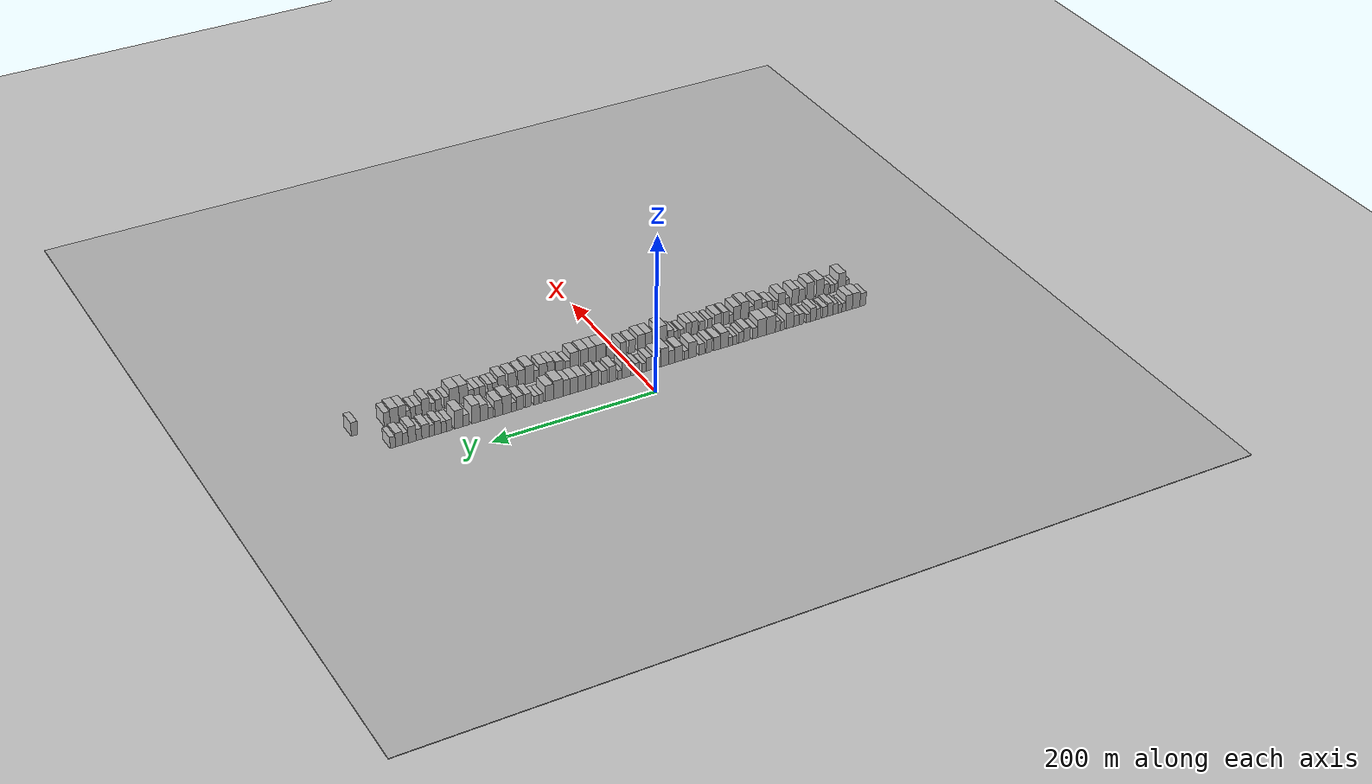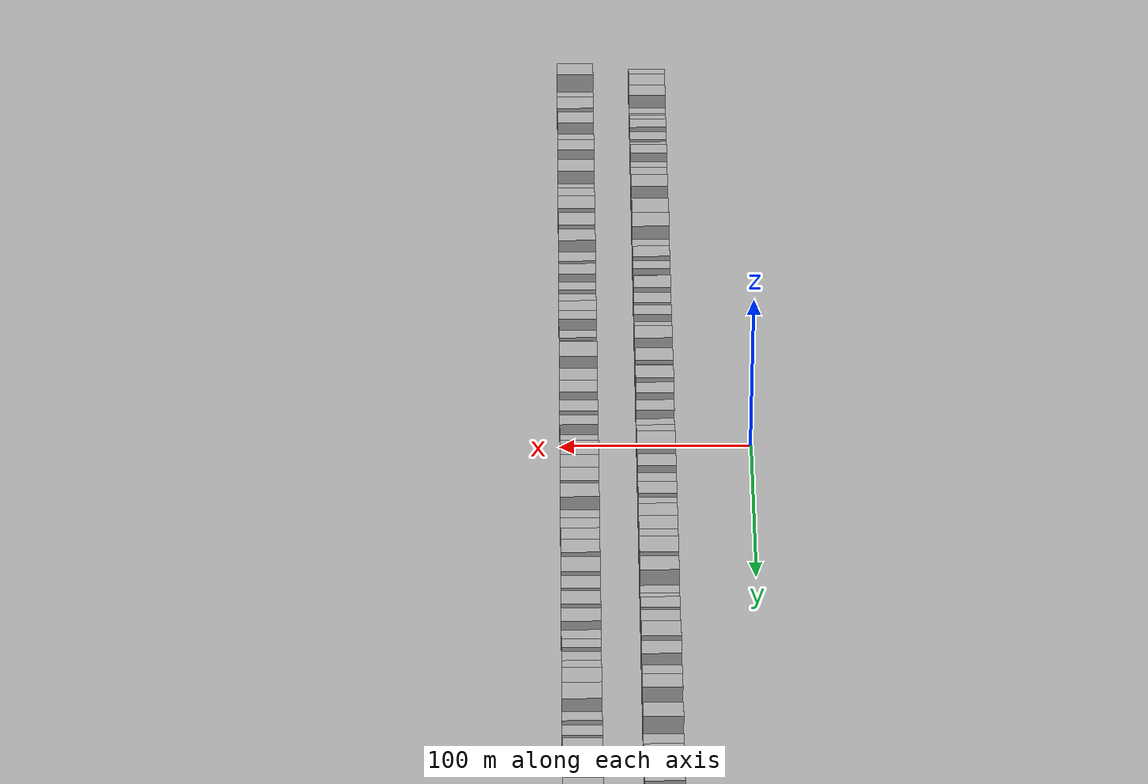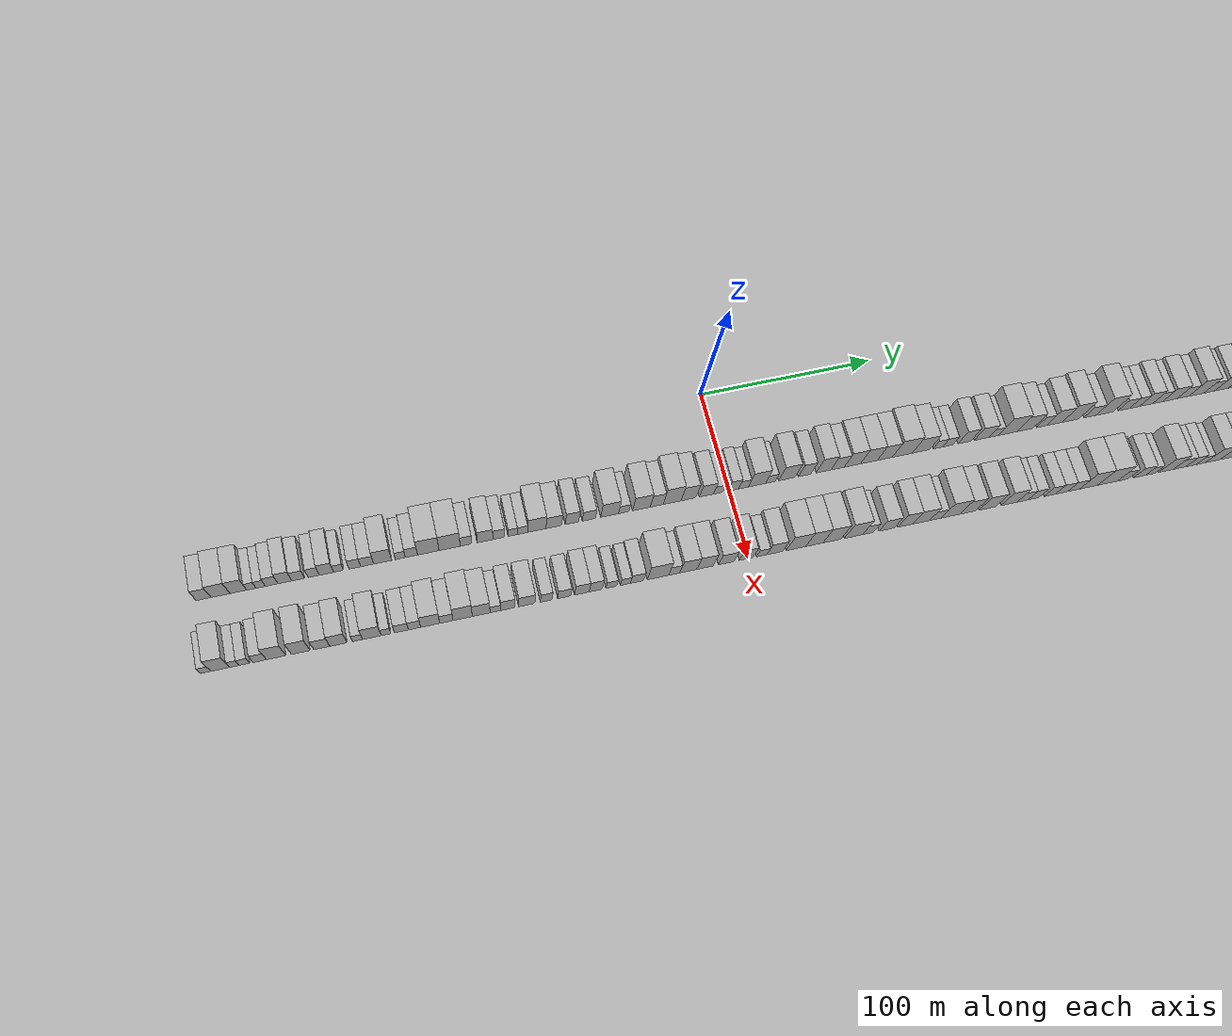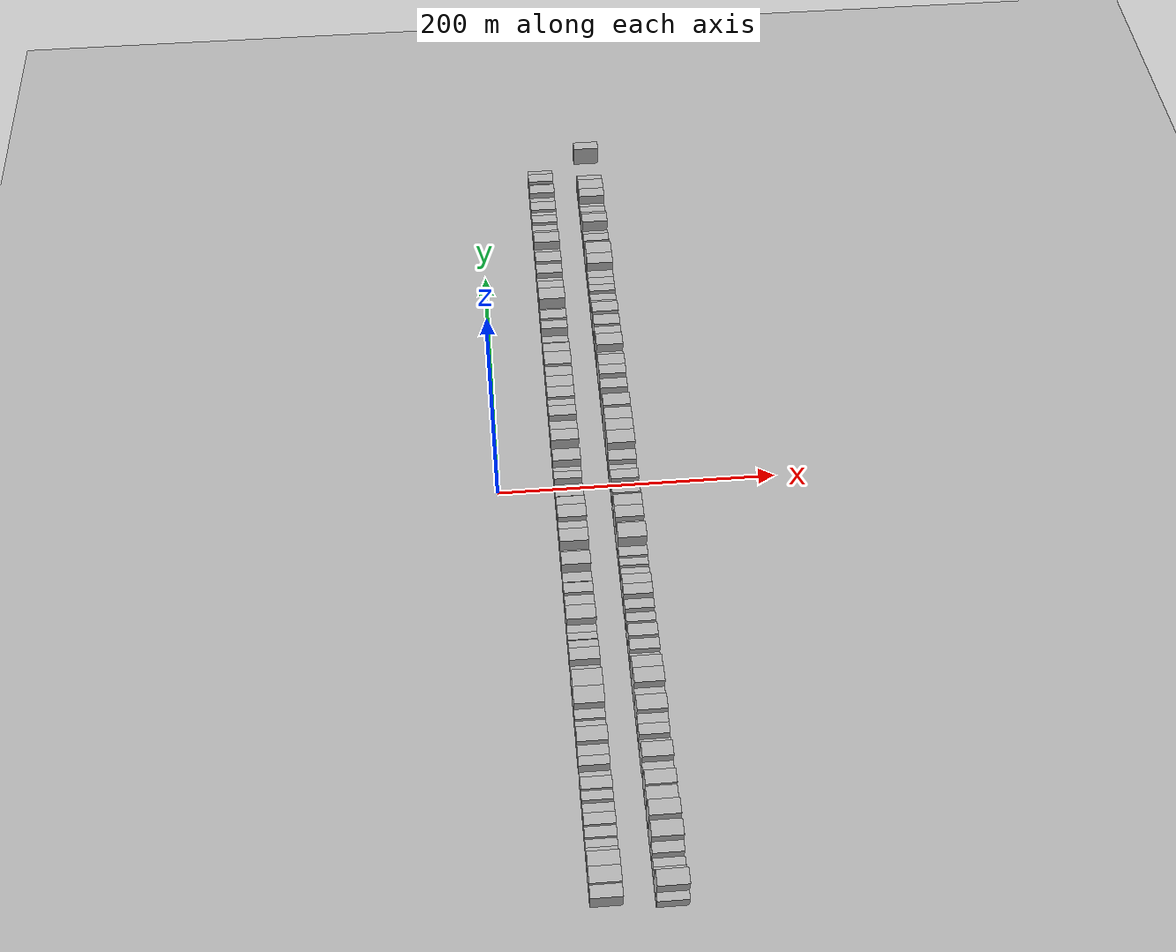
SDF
<?xml version="1.0" encoding="utf-8"?>

<sdf version="1.6">

   <world name="default">

      <gui fullscreen="0">

         <camera name="user_camera">

            <pose>-15 0 4.57585 0 0 0</pose>

            <view_controller>orbit</view_controller>

         </camera>

      </gui>

      <scene>

         <sky>

           <clouds>

             <speed>12</speed>

           </clouds>

         </sky>

         <ambient>0.4 0.4 0.4 1</ambient>

         <background>0.7 0.7 0.7 1</background>

         <shadows>1</shadows>

      </scene>

      <gravity>0 0 -9.8066</gravity>

      <magnetic_field>6e-06 2.3e-05 -4.2e-05</magnetic_field>

      <physics default="0" name="default_physics" type="ode">

         <ode>

            <solver>

               <type>quick</type>

               <iters>10</iters>

               <sor>1.0</sor>

               <use_dynamic_moi_rescaling>0</use_dynamic_moi_rescaling>

            </solver>

            <constraints>

               <cfm>0</cfm>

               <erp>0.2</erp>

               <contact_max_correcting_vel>100</contact_max_correcting_vel>

               <contact_surface_layer>0.001</contact_surface_layer>

            </constraints>

         </ode>

         <max_step_size>0.004</max_step_size>

         <real_time_factor>1</real_time_factor>

         <real_time_update_rate>250</real_time_update_rate>

      </physics>

      <light name="sun" type="directional">

         <cast_shadows>1</cast_shadows>

         <pose>0 0 10 0 0 0</pose>

         <diffuse>0.8 0.8 0.8 1</diffuse>

         <specular>0.2 0.2 0.2 1</specular>

         <attenuation>

            <range>1000</range>

            <constant>0.9</constant>

            <linear>0.01</linear>

            <quadratic>0.001</quadratic>

         </attenuation>

         <direction>-0.5 0.1 -0.9</direction>

      </light>

      <include>

         <name>ground_plane_1</name>

         <uri>model://HANNAS_ground_plane</uri>

         <pose>0 0 0  0 0 0</pose>

      </include>

      <include>

         <name>ground_plane_2</name>

         <uri>model://HANNAS_ground_plane</uri>

         <pose>100 0 0  0 0 0</pose>

      </include>

      <model name="building_1">

         <static>1</static>

         <pose frame="">50.0000 -292.9607 0 0.000000 0.000000 0.000000</pose>

         <link name="link">

            <pose frame="">0 0 9.00 0 0 0</pose>

            <collision name="collision">

               <geometry>

                  <box>

                     <size>20.0000 8.0786 18.0000</size>

                  </box>

               </geometry>

               <max_contacts>10</max_contacts>

               <surface>

                  <contact>

                     <ode/>

                  </contact>

                  <bounce/>

                  <friction>

                     <torsional>

                        <ode/>

                     </torsional>

                     <ode/>

                  </friction>

               </surface>

            </collision>

            <visual name="visual">

               <cast_shadows>0</cast_shadows>

               <geometry>

                  <box>

                     <size>20.0000 8.0786 18.0000</size>

                  </box>

               </geometry>

               <material>

                  <script>

                     <uri>model://HANNAS_wall/materials/scripts</uri>

                     <uri>model://HANNAS_wall/materials/textures</uri>

                     <name>vrc/HANNAS_wall</name>

                  </script>

               </material>

            </visual>

            <self_collide>0</self_collide>

            <enable_wind>0</enable_wind>

            <kinematic>0</kinematic>

         </link>

      </model>

      <model name="building_2">

         <static>1</static>

         <pose frame="">50.0000 -283.7995 0 0.000000 0.000000 0.000000</pose>

         <link name="link">

            <pose frame="">0 0 10.50 0 0 0</pose>

            <collision name="collision">

               <geometry>

                  <box>

                     <size>20.0000 10.2437 21.0000</size>

                  </box>

               </geometry>

               <max_contacts>10</max_contacts>

               <surface>

                  <contact>

                     <ode/>

                  </contact>

                  <bounce/>

                  <friction>

                     <torsional>

                        <ode/>

                     </torsional>

                     <ode/>

                  </friction>

               </surface>

            </collision>

            <visual name="visual">

               <cast_shadows>0</cast_shadows>

               <geometry>

                  <box>

                     <size>20.0000 10.2437 21.0000</size>

                  </box>

               </geometry>

               <material>

                  <script>

                     <uri>model://HANNAS_wall/materials/scripts</uri>

                     <uri>model://HANNAS_wall/materials/textures</uri>

                     <name>vrc/HANNAS_wall</name>

                  </script>

               </material>

            </visual>

            <self_collide>0</self_collide>

            <enable_wind>0</enable_wind>

            <kinematic>0</kinematic>

         </link>

      </model>

      <model name="building_3">

         <static>1</static>

         <pose frame="">50.0000 -274.1064 0 0.000000 0.000000 0.000000</pose>

         <link name="link">

            <pose frame="">0 0 10.50 0 0 0</pose>

            <collision name="collision">

               <geometry>

                  <box>

                     <size>20.0000 9.1425 21.0000</size>

                  </box>

               </geometry>

               <max_contacts>10</max_contacts>

               <surface>

                  <contact>

                     <ode/>

                  </contact>

                  <bounce/>

                  <friction>

                     <torsional>

                        <ode/>

                     </torsional>

                     <ode/>

                  </friction>

               </surface>

            </collision>

            <visual name="visual">

               <cast_shadows>0</cast_shadows>

               <geometry>

                  <box>

                     <size>20.0000 9.1425 21.0000</size>

                  </box>

               </geometry>

               <material>

                  <script>

                     <uri>model://HANNAS_wall/materials/scripts</uri>

                     <uri>model://HANNAS_wall/materials/textures</uri>

                     <name>vrc/HANNAS_wall</name>

                  </script>

               </material>

            </visual>

            <self_collide>0</self_collide>

            <enable_wind>0</enable_wind>

            <kinematic>0</kinematic>

         </link>

      </model>

      <model name="building_4">

         <static>1</static>

         <pose frame="">50.0000 -267.0367 0 0.000000 0.000000 0.000000</pose>

         <link name="link">

            <pose frame="">0 0 6.00 0 0 0</pose>

            <collision name="collision">

               <geometry>

                  <box>

                     <size>20.0000 4.9970 12.0000</size>

                  </box>

               </geometry>

               <max_contacts>10</max_contacts>

               <surface>

                  <contact>

                     <ode/>

                  </contact>

                  <bounce/>

                  <friction>

                     <torsional>

                        <ode/>

                     </torsional>

                     <ode/>

                  </friction>

               </surface>

            </collision>

            <visual name="visual">

               <cast_shadows>0</cast_shadows>

               <geometry>

                  <box>

                     <size>20.0000 4.9970 12.0000</size>

                  </box>

               </geometry>

               <material>

                  <script>

                     <uri>model://HANNAS_wall/materials/scripts</uri>

                     <uri>model://HANNAS_wall/materials/textures</uri>

                     <name>vrc/HANNAS_wall</name>

                  </script>

               </material>

            </visual>

            <self_collide>0</self_collide>

            <enable_wind>0</enable_wind>

            <kinematic>0</kinematic>

         </link>

      </model>

      <model name="building_5">

         <static>1</static>

         <pose frame="">50.0000 -261.9520 0 0.000000 0.000000 0.000000</pose>

         <link name="link">

            <pose frame="">0 0 6.00 0 0 0</pose>

            <collision name="collision">

               <geometry>

                  <box>

                     <size>20.0000 5.1724 12.0000</size>

                  </box>

               </geometry>

               <max_contacts>10</max_contacts>

               <surface>

                  <contact>

                     <ode/>

                  </contact>

                  <bounce/>

                  <friction>

                     <torsional>

                        <ode/>

                     </torsional>

                     <ode/>

                  </friction>

               </surface>

            </collision>

            <visual name="visual">

               <cast_shadows>0</cast_shadows>

               <geometry>

                  <box>

                     <size>20.0000 5.1724 12.0000</size>

                  </box>

               </geometry>

               <material>

                  <script>

                     <uri>model://HANNAS_wall/materials/scripts</uri>

                     <uri>model://HANNAS_wall/materials/textures</uri>

                     <name>vrc/HANNAS_wall</name>

                  </script>

               </material>

            </visual>

            <self_collide>0</self_collide>

            <enable_wind>0</enable_wind>

            <kinematic>0</kinematic>

         </link>

      </model>

      <model name="building_6">

         <static>1</static>

         <pose frame="">50.0000 -255.9389 0 0.000000 0.000000 0.000000</pose>

         <link name="link">

            <pose frame="">0 0 7.50 0 0 0</pose>

            <collision name="collision">

               <geometry>

                  <box>

                     <size>20.0000 6.8538 15.0000</size>

                  </box>

               </geometry>

               <max_contacts>10</max_contacts>

               <surface>

                  <contact>

                     <ode/>

                  </contact>

                  <bounce/>

                  <friction>

                     <torsional>

                        <ode/>

                     </torsional>

                     <ode/>

                  </friction>

               </surface>

            </collision>

            <visual name="visual">

               <cast_shadows>0</cast_shadows>

               <geometry>

                  <box>

                     <size>20.0000 6.8538 15.0000</size>

                  </box>

               </geometry>

               <material>

                  <script>

                     <uri>model://HANNAS_wall/materials/scripts</uri>

                     <uri>model://HANNAS_wall/materials/textures</uri>

                     <name>vrc/HANNAS_wall</name>

                  </script>

               </material>

            </visual>

            <self_collide>0</self_collide>

            <enable_wind>0</enable_wind>

            <kinematic>0</kinematic>

         </link>

      </model>

      <model name="building_7">

         <static>1</static>

         <pose frame="">50.0000 -248.7187 0 0.000000 0.000000 0.000000</pose>

         <link name="link">

            <pose frame="">0 0 9.00 0 0 0</pose>

            <collision name="collision">

               <geometry>

                  <box>

                     <size>20.0000 7.5866 18.0000</size>

                  </box>

               </geometry>

               <max_contacts>10</max_contacts>

               <surface>

                  <contact>

                     <ode/>

                  </contact>

                  <bounce/>

                  <friction>

                     <torsional>

                        <ode/>

                     </torsional>

                     <ode/>

                  </friction>

               </surface>

            </collision>

            <visual name="visual">

               <cast_shadows>0</cast_shadows>

               <geometry>

                  <box>

                     <size>20.0000 7.5866 18.0000</size>

                  </box>

               </geometry>

               <material>

                  <script>

                     <uri>model://HANNAS_wall/materials/scripts</uri>

                     <uri>model://HANNAS_wall/materials/textures</uri>

                     <name>vrc/HANNAS_wall</name>

                  </script>

               </material>

            </visual>

            <self_collide>0</self_collide>

            <enable_wind>0</enable_wind>

            <kinematic>0</kinematic>

         </link>

      </model>

      <model name="building_8">

         <static>1</static>

         <pose frame="">50.0000 -241.4648 0 0.000000 0.000000 0.000000</pose>

         <link name="link">

            <pose frame="">0 0 7.50 0 0 0</pose>

            <collision name="collision">

               <geometry>

                  <box>

                     <size>20.0000 6.9213 15.0000</size>

                  </box>

               </geometry>

               <max_contacts>10</max_contacts>

               <surface>

                  <contact>

                     <ode/>

                  </contact>

                  <bounce/>

                  <friction>

                     <torsional>

                        <ode/>

                     </torsional>

                     <ode/>

                  </friction>

               </surface>

            </collision>

            <visual name="visual">

               <cast_shadows>0</cast_shadows>

               <geometry>

                  <box>

                     <size>20.0000 6.9213 15.0000</size>

                  </box>

               </geometry>

               <material>

                  <script>

                     <uri>model://HANNAS_wall/materials/scripts</uri>

                     <uri>model://HANNAS_wall/materials/textures</uri>

                     <name>vrc/HANNAS_wall</name>

                  </script>

               </material>

            </visual>

            <self_collide>0</self_collide>

            <enable_wind>0</enable_wind>

            <kinematic>0</kinematic>

         </link>

      </model>

      <model name="building_9">

         <static>1</static>

         <pose frame="">50.0000 -232.9255 0 0.000000 0.000000 0.000000</pose>

         <link name="link">

            <pose frame="">0 0 7.50 0 0 0</pose>

            <collision name="collision">

               <geometry>

                  <box>

                     <size>20.0000 6.1572 15.0000</size>

                  </box>

               </geometry>

               <max_contacts>10</max_contacts>

               <surface>

                  <contact>

                     <ode/>

                  </contact>

                  <bounce/>

                  <friction>

                     <torsional>

                        <ode/>

                     </torsional>

                     <ode/>

                  </friction>

               </surface>

            </collision>

            <visual name="visual">

               <cast_shadows>0</cast_shadows>

               <geometry>

                  <box>

                     <size>20.0000 6.1572 15.0000</size>

                  </box>

               </geometry>

               <material>

                  <script>

                     <uri>model://HANNAS_wall/materials/scripts</uri>

                     <uri>model://HANNAS_wall/materials/textures</uri>

                     <name>vrc/HANNAS_wall</name>

                  </script>

               </material>

            </visual>

            <self_collide>0</self_collide>

            <enable_wind>0</enable_wind>

            <kinematic>0</kinematic>

         </link>

      </model>

      <model name="building_10">

         <static>1</static>

         <pose frame="">50.0000 -225.9368 0 0.000000 0.000000 0.000000</pose>

         <link name="link">

            <pose frame="">0 0 9.00 0 0 0</pose>

            <collision name="collision">

               <geometry>

                  <box>

                     <size>20.0000 7.8204 18.0000</size>

                  </box>

               </geometry>

               <max_contacts>10</max_contacts>

               <surface>

                  <contact>

                     <ode/>

                  </contact>

                  <bounce/>

                  <friction>

                     <torsional>

                        <ode/>

                     </torsional>

                     <ode/>

                  </friction>

               </surface>

            </collision>

            <visual name="visual">

               <cast_shadows>0</cast_shadows>

               <geometry>

                  <box>

                     <size>20.0000 7.8204 18.0000</size>

                  </box>

               </geometry>

               <material>

                  <script>

                     <uri>model://HANNAS_wall/materials/scripts</uri>

                     <uri>model://HANNAS_wall/materials/textures</uri>

                     <name>vrc/HANNAS_wall</name>

                  </script>

               </material>

            </visual>

            <self_collide>0</self_collide>

            <enable_wind>0</enable_wind>

            <kinematic>0</kinematic>

         </link>

      </model>

      <model name="building_11">

         <static>1</static>

         <pose frame="">50.0000 -219.2824 0 0.000000 0.000000 0.000000</pose>

         <link name="link">

            <pose frame="">0 0 6.00 0 0 0</pose>

            <collision name="collision">

               <geometry>

                  <box>

                     <size>20.0000 5.4883 12.0000</size>

                  </box>

               </geometry>

               <max_contacts>10</max_contacts>

               <surface>

                  <contact>

                     <ode/>

                  </contact>

                  <bounce/>

                  <friction>

                     <torsional>

                        <ode/>

                     </torsional>

                     <ode/>

                  </friction>

               </surface>

            </collision>

            <visual name="visual">

               <cast_shadows>0</cast_shadows>

               <geometry>

                  <box>

                     <size>20.0000 5.4883 12.0000</size>

                  </box>

               </geometry>

               <material>

                  <script>

                     <uri>model://HANNAS_wall/materials/scripts</uri>

                     <uri>model://HANNAS_wall/materials/textures</uri>

                     <name>vrc/HANNAS_wall</name>

                  </script>

               </material>

            </visual>

            <self_collide>0</self_collide>

            <enable_wind>0</enable_wind>

            <kinematic>0</kinematic>

         </link>

      </model>

      <model name="building_12">

         <static>1</static>

         <pose frame="">50.0000 -210.3345 0 0.000000 0.000000 0.000000</pose>

         <link name="link">

            <pose frame="">0 0 7.50 0 0 0</pose>

            <collision name="collision">

               <geometry>

                  <box>

                     <size>20.0000 6.4076 15.0000</size>

                  </box>

               </geometry>

               <max_contacts>10</max_contacts>

               <surface>

                  <contact>

                     <ode/>

                  </contact>

                  <bounce/>

                  <friction>

                     <torsional>

                        <ode/>

                     </torsional>

                     <ode/>

                  </friction>

               </surface>

            </collision>

            <visual name="visual">

               <cast_shadows>0</cast_shadows>

               <geometry>

                  <box>

                     <size>20.0000 6.4076 15.0000</size>

                  </box>

               </geometry>

               <material>

                  <script>

                     <uri>model://HANNAS_wall/materials/scripts</uri>

                     <uri>model://HANNAS_wall/materials/textures</uri>

                     <name>vrc/HANNAS_wall</name>

                  </script>

               </material>

            </visual>

            <self_collide>0</self_collide>

            <enable_wind>0</enable_wind>

            <kinematic>0</kinematic>

         </link>

      </model>

      <model name="building_13">

         <static>1</static>

         <pose frame="">50.0000 -203.5243 0 0.000000 0.000000 0.000000</pose>

         <link name="link">

            <pose frame="">0 0 7.50 0 0 0</pose>

            <collision name="collision">

               <geometry>

                  <box>

                     <size>20.0000 7.2128 15.0000</size>

                  </box>

               </geometry>

               <max_contacts>10</max_contacts>

               <surface>

                  <contact>

                     <ode/>

                  </contact>

                  <bounce/>

                  <friction>

                     <torsional>

                        <ode/>

                     </torsional>

                     <ode/>

                  </friction>

               </surface>

            </collision>

            <visual name="visual">

               <cast_shadows>0</cast_shadows>

               <geometry>

                  <box>

                     <size>20.0000 7.2128 15.0000</size>

                  </box>

               </geometry>

               <material>

                  <script>

                     <uri>model://HANNAS_wall/materials/scripts</uri>

                     <uri>model://HANNAS_wall/materials/textures</uri>

                     <name>vrc/HANNAS_wall</name>

                  </script>

               </material>

            </visual>

            <self_collide>0</self_collide>

            <enable_wind>0</enable_wind>

            <kinematic>0</kinematic>

         </link>

      </model>

      <model name="building_14">

         <static>1</static>

         <pose frame="">50.0000 -194.9490 0 0.000000 0.000000 0.000000</pose>

         <link name="link">

            <pose frame="">0 0 10.50 0 0 0</pose>

            <collision name="collision">

               <geometry>

                  <box>

                     <size>20.0000 9.9377 21.0000</size>

                  </box>

               </geometry>

               <max_contacts>10</max_contacts>

               <surface>

                  <contact>

                     <ode/>

                  </contact>

                  <bounce/>

                  <friction>

                     <torsional>

                        <ode/>

                     </torsional>

                     <ode/>

                  </friction>

               </surface>

            </collision>

            <visual name="visual">

               <cast_shadows>0</cast_shadows>

               <geometry>

                  <box>

                     <size>20.0000 9.9377 21.0000</size>

                  </box>

               </geometry>

               <material>

                  <script>

                     <uri>model://HANNAS_wall/materials/scripts</uri>

                     <uri>model://HANNAS_wall/materials/textures</uri>

                     <name>vrc/HANNAS_wall</name>

                  </script>

               </material>

            </visual>

            <self_collide>0</self_collide>

            <enable_wind>0</enable_wind>

            <kinematic>0</kinematic>

         </link>

      </model>

      <model name="building_15">

         <static>1</static>

         <pose frame="">50.0000 -185.2317 0 0.000000 0.000000 0.000000</pose>

         <link name="link">

            <pose frame="">0 0 6.00 0 0 0</pose>

            <collision name="collision">

               <geometry>

                  <box>

                     <size>20.0000 5.4968 12.0000</size>

                  </box>

               </geometry>

               <max_contacts>10</max_contacts>

               <surface>

                  <contact>

                     <ode/>

                  </contact>

                  <bounce/>

                  <friction>

                     <torsional>

                        <ode/>

                     </torsional>

                     <ode/>

                  </friction>

               </surface>

            </collision>

            <visual name="visual">

               <cast_shadows>0</cast_shadows>

               <geometry>

                  <box>

                     <size>20.0000 5.4968 12.0000</size>

                  </box>

               </geometry>

               <material>

                  <script>

                     <uri>model://HANNAS_wall/materials/scripts</uri>

                     <uri>model://HANNAS_wall/materials/textures</uri>

                     <name>vrc/HANNAS_wall</name>

                  </script>

               </material>

            </visual>

            <self_collide>0</self_collide>

            <enable_wind>0</enable_wind>

            <kinematic>0</kinematic>

         </link>

      </model>

      <model name="building_16">

         <static>1</static>

         <pose frame="">50.0000 -179.1196 0 0.000000 0.000000 0.000000</pose>

         <link name="link">

            <pose frame="">0 0 7.50 0 0 0</pose>

            <collision name="collision">

               <geometry>

                  <box>

                     <size>20.0000 6.7274 15.0000</size>

                  </box>

               </geometry>

               <max_contacts>10</max_contacts>

               <surface>

                  <contact>

                     <ode/>

                  </contact>

                  <bounce/>

                  <friction>

                     <torsional>

                        <ode/>

                     </torsional>

                     <ode/>

                  </friction>

               </surface>

            </collision>

            <visual name="visual">

               <cast_shadows>0</cast_shadows>

               <geometry>

                  <box>

                     <size>20.0000 6.7274 15.0000</size>

                  </box>

               </geometry>

               <material>

                  <script>

                     <uri>model://HANNAS_wall/materials/scripts</uri>

                     <uri>model://HANNAS_wall/materials/textures</uri>

                     <name>vrc/HANNAS_wall</name>

                  </script>

               </material>

            </visual>

            <self_collide>0</self_collide>

            <enable_wind>0</enable_wind>

            <kinematic>0</kinematic>

         </link>

      </model>

      <model name="building_17">

         <static>1</static>

         <pose frame="">50.0000 -169.7730 0 0.000000 0.000000 0.000000</pose>

         <link name="link">

            <pose frame="">0 0 12.00 0 0 0</pose>

            <collision name="collision">

               <geometry>

                  <box>

                     <size>20.0000 11.9657 24.0000</size>

                  </box>

               </geometry>

               <max_contacts>10</max_contacts>

               <surface>

                  <contact>

                     <ode/>

                  </contact>

                  <bounce/>

                  <friction>

                     <torsional>

                        <ode/>

                     </torsional>

                     <ode/>

                  </friction>

               </surface>

            </collision>

            <visual name="visual">

               <cast_shadows>0</cast_shadows>

               <geometry>

                  <box>

                     <size>20.0000 11.9657 24.0000</size>

                  </box>

               </geometry>

               <material>

                  <script>

                     <uri>model://HANNAS_wall/materials/scripts</uri>

                     <uri>model://HANNAS_wall/materials/textures</uri>

                     <name>vrc/HANNAS_wall</name>

                  </script>

               </material>

            </visual>

            <self_collide>0</self_collide>

            <enable_wind>0</enable_wind>

            <kinematic>0</kinematic>

         </link>

      </model>

      <model name="building_18">

         <static>1</static>

         <pose frame="">50.0000 -157.8910 0 0.000000 0.000000 0.000000</pose>

         <link name="link">

            <pose frame="">0 0 12.00 0 0 0</pose>

            <collision name="collision">

               <geometry>

                  <box>

                     <size>20.0000 11.7985 24.0000</size>

                  </box>

               </geometry>

               <max_contacts>10</max_contacts>

               <surface>

                  <contact>

                     <ode/>

                  </contact>

                  <bounce/>

                  <friction>

                     <torsional>

                        <ode/>

                     </torsional>

                     <ode/>

                  </friction>

               </surface>

            </collision>

            <visual name="visual">

               <cast_shadows>0</cast_shadows>

               <geometry>

                  <box>

                     <size>20.0000 11.7985 24.0000</size>

                  </box>

               </geometry>

               <material>

                  <script>

                     <uri>model://HANNAS_wall/materials/scripts</uri>

                     <uri>model://HANNAS_wall/materials/textures</uri>

                     <name>vrc/HANNAS_wall</name>

                  </script>

               </material>

            </visual>

            <self_collide>0</self_collide>

            <enable_wind>0</enable_wind>

            <kinematic>0</kinematic>

         </link>

      </model>

      <model name="building_19">

         <static>1</static>

         <pose frame="">50.0000 -148.7655 0 0.000000 0.000000 0.000000</pose>

         <link name="link">

            <pose frame="">0 0 7.50 0 0 0</pose>

            <collision name="collision">

               <geometry>

                  <box>

                     <size>20.0000 6.4524 15.0000</size>

                  </box>

               </geometry>

               <max_contacts>10</max_contacts>

               <surface>

                  <contact>

                     <ode/>

                  </contact>

                  <bounce/>

                  <friction>

                     <torsional>

                        <ode/>

                     </torsional>

                     <ode/>

                  </friction>

               </surface>

            </collision>

            <visual name="visual">

               <cast_shadows>0</cast_shadows>

               <geometry>

                  <box>

                     <size>20.0000 6.4524 15.0000</size>

                  </box>

               </geometry>

               <material>

                  <script>

                     <uri>model://HANNAS_wall/materials/scripts</uri>

                     <uri>model://HANNAS_wall/materials/textures</uri>

                     <name>vrc/HANNAS_wall</name>

                  </script>

               </material>

            </visual>

            <self_collide>0</self_collide>

            <enable_wind>0</enable_wind>

            <kinematic>0</kinematic>

         </link>

      </model>

      <model name="building_20">

         <static>1</static>

         <pose frame="">50.0000 -138.1742 0 0.000000 0.000000 0.000000</pose>

         <link name="link">

            <pose frame="">0 0 9.00 0 0 0</pose>

            <collision name="collision">

               <geometry>

                  <box>

                     <size>20.0000 8.7303 18.0000</size>

                  </box>

               </geometry>

               <max_contacts>10</max_contacts>

               <surface>

                  <contact>

                     <ode/>

                  </contact>

                  <bounce/>

                  <friction>

                     <torsional>

                        <ode/>

                     </torsional>

                     <ode/>

                  </friction>

               </surface>

            </collision>

            <visual name="visual">

               <cast_shadows>0</cast_shadows>

               <geometry>

                  <box>

                     <size>20.0000 8.7303 18.0000</size>

                  </box>

               </geometry>

               <material>

                  <script>

                     <uri>model://HANNAS_wall/materials/scripts</uri>

                     <uri>model://HANNAS_wall/materials/textures</uri>

                     <name>vrc/HANNAS_wall</name>

                  </script>

               </material>

            </visual>

            <self_collide>0</self_collide>

            <enable_wind>0</enable_wind>

            <kinematic>0</kinematic>

         </link>

      </model>

      <model name="building_21">

         <static>1</static>

         <pose frame="">50.0000 -130.5213 0 0.000000 0.000000 0.000000</pose>

         <link name="link">

            <pose frame="">0 0 7.50 0 0 0</pose>

            <collision name="collision">

               <geometry>

                  <box>

                     <size>20.0000 6.5754 15.0000</size>

                  </box>

               </geometry>

               <max_contacts>10</max_contacts>

               <surface>

                  <contact>

                     <ode/>

                  </contact>

                  <bounce/>

                  <friction>

                     <torsional>

                        <ode/>

                     </torsional>

                     <ode/>

                  </friction>

               </surface>

            </collision>

            <visual name="visual">

               <cast_shadows>0</cast_shadows>

               <geometry>

                  <box>

                     <size>20.0000 6.5754 15.0000</size>

                  </box>

               </geometry>

               <material>

                  <script>

                     <uri>model://HANNAS_wall/materials/scripts</uri>

                     <uri>model://HANNAS_wall/materials/textures</uri>

                     <name>vrc/HANNAS_wall</name>

                  </script>

               </material>

            </visual>

            <self_collide>0</self_collide>

            <enable_wind>0</enable_wind>

            <kinematic>0</kinematic>

         </link>

      </model>

      <model name="building_22">

         <static>1</static>

         <pose frame="">50.0000 -122.6675 0 0.000000 0.000000 0.000000</pose>

         <link name="link">

            <pose frame="">0 0 6.00 0 0 0</pose>

            <collision name="collision">

               <geometry>

                  <box>

                     <size>20.0000 5.1323 12.0000</size>

                  </box>

               </geometry>

               <max_contacts>10</max_contacts>

               <surface>

                  <contact>

                     <ode/>

                  </contact>

                  <bounce/>

                  <friction>

                     <torsional>

                        <ode/>

                     </torsional>

                     <ode/>

                  </friction>

               </surface>

            </collision>

            <visual name="visual">

               <cast_shadows>0</cast_shadows>

               <geometry>

                  <box>

                     <size>20.0000 5.1323 12.0000</size>

                  </box>

               </geometry>

               <material>

                  <script>

                     <uri>model://HANNAS_wall/materials/scripts</uri>

                     <uri>model://HANNAS_wall/materials/textures</uri>

                     <name>vrc/HANNAS_wall</name>

                  </script>

               </material>

            </visual>

            <self_collide>0</self_collide>

            <enable_wind>0</enable_wind>

            <kinematic>0</kinematic>

         </link>

      </model>

      <model name="building_23">

         <static>1</static>

         <pose frame="">50.0000 -117.2452 0 0.000000 0.000000 0.000000</pose>

         <link name="link">

            <pose frame="">0 0 6.00 0 0 0</pose>

            <collision name="collision">

               <geometry>

                  <box>

                     <size>20.0000 5.7124 12.0000</size>

                  </box>

               </geometry>

               <max_contacts>10</max_contacts>

               <surface>

                  <contact>

                     <ode/>

                  </contact>

                  <bounce/>

                  <friction>

                     <torsional>

                        <ode/>

                     </torsional>

                     <ode/>

                  </friction>

               </surface>

            </collision>

            <visual name="visual">

               <cast_shadows>0</cast_shadows>

               <geometry>

                  <box>

                     <size>20.0000 5.7124 12.0000</size>

                  </box>

               </geometry>

               <material>

                  <script>

                     <uri>model://HANNAS_wall/materials/scripts</uri>

                     <uri>model://HANNAS_wall/materials/textures</uri>

                     <name>vrc/HANNAS_wall</name>

                  </script>

               </material>

            </visual>

            <self_collide>0</self_collide>

            <enable_wind>0</enable_wind>

            <kinematic>0</kinematic>

         </link>

      </model>

      <model name="building_24">

         <static>1</static>

         <pose frame="">50.0000 -109.2051 0 0.000000 0.000000 0.000000</pose>

         <link name="link">

            <pose frame="">0 0 10.50 0 0 0</pose>

            <collision name="collision">

               <geometry>

                  <box>

                     <size>20.0000 10.3678 21.0000</size>

                  </box>

               </geometry>

               <max_contacts>10</max_contacts>

               <surface>

                  <contact>

                     <ode/>

                  </contact>

                  <bounce/>

                  <friction>

                     <torsional>

                        <ode/>

                     </torsional>

                     <ode/>

                  </friction>

               </surface>

            </collision>

            <visual name="visual">

               <cast_shadows>0</cast_shadows>

               <geometry>

                  <box>

                     <size>20.0000 10.3678 21.0000</size>

                  </box>

               </geometry>

               <material>

                  <script>

                     <uri>model://HANNAS_wall/materials/scripts</uri>

                     <uri>model://HANNAS_wall/materials/textures</uri>

                     <name>vrc/HANNAS_wall</name>

                  </script>

               </material>

            </visual>

            <self_collide>0</self_collide>

            <enable_wind>0</enable_wind>

            <kinematic>0</kinematic>

         </link>

      </model>

      <model name="building_25">

         <static>1</static>

         <pose frame="">50.0000 -99.6082 0 0.000000 0.000000 0.000000</pose>

         <link name="link">

            <pose frame="">0 0 9.00 0 0 0</pose>

            <collision name="collision">

               <geometry>

                  <box>

                     <size>20.0000 8.8259 18.0000</size>

                  </box>

               </geometry>

               <max_contacts>10</max_contacts>

               <surface>

                  <contact>

                     <ode/>

                  </contact>

                  <bounce/>

                  <friction>

                     <torsional>

                        <ode/>

                     </torsional>

                     <ode/>

                  </friction>

               </surface>

            </collision>

            <visual name="visual">

               <cast_shadows>0</cast_shadows>

               <geometry>

                  <box>

                     <size>20.0000 8.8259 18.0000</size>

                  </box>

               </geometry>

               <material>

                  <script>

                     <uri>model://HANNAS_wall/materials/scripts</uri>

                     <uri>model://HANNAS_wall/materials/textures</uri>

                     <name>vrc/HANNAS_wall</name>

                  </script>

               </material>

            </visual>

            <self_collide>0</self_collide>

            <enable_wind>0</enable_wind>

            <kinematic>0</kinematic>

         </link>

      </model>

      <model name="building_26">

         <static>1</static>

         <pose frame="">50.0000 -89.3724 0 0.000000 0.000000 0.000000</pose>

         <link name="link">

            <pose frame="">0 0 9.00 0 0 0</pose>

            <collision name="collision">

               <geometry>

                  <box>

                     <size>20.0000 7.6458 18.0000</size>

                  </box>

               </geometry>

               <max_contacts>10</max_contacts>

               <surface>

                  <contact>

                     <ode/>

                  </contact>

                  <bounce/>

                  <friction>

                     <torsional>

                        <ode/>

                     </torsional>

                     <ode/>

                  </friction>

               </surface>

            </collision>

            <visual name="visual">

               <cast_shadows>0</cast_shadows>

               <geometry>

                  <box>

                     <size>20.0000 7.6458 18.0000</size>

                  </box>

               </geometry>

               <material>

                  <script>

                     <uri>model://HANNAS_wall/materials/scripts</uri>

                     <uri>model://HANNAS_wall/materials/textures</uri>

                     <name>vrc/HANNAS_wall</name>

                  </script>

               </material>

            </visual>

            <self_collide>0</self_collide>

            <enable_wind>0</enable_wind>

            <kinematic>0</kinematic>

         </link>

      </model>

      <model name="building_27">

         <static>1</static>

         <pose frame="">50.0000 -79.8591 0 0.000000 0.000000 0.000000</pose>

         <link name="link">

            <pose frame="">0 0 7.50 0 0 0</pose>

            <collision name="collision">

               <geometry>

                  <box>

                     <size>20.0000 7.3808 15.0000</size>

                  </box>

               </geometry>

               <max_contacts>10</max_contacts>

               <surface>

                  <contact>

                     <ode/>

                  </contact>

                  <bounce/>

                  <friction>

                     <torsional>

                        <ode/>

                     </torsional>

                     <ode/>

                  </friction>

               </surface>

            </collision>

            <visual name="visual">

               <cast_shadows>0</cast_shadows>

               <geometry>

                  <box>

                     <size>20.0000 7.3808 15.0000</size>

                  </box>

               </geometry>

               <material>

                  <script>

                     <uri>model://HANNAS_wall/materials/scripts</uri>

                     <uri>model://HANNAS_wall/materials/textures</uri>

                     <name>vrc/HANNAS_wall</name>

                  </script>

               </material>

            </visual>

            <self_collide>0</self_collide>

            <enable_wind>0</enable_wind>

            <kinematic>0</kinematic>

         </link>

      </model>

      <model name="building_28">

         <static>1</static>

         <pose frame="">50.0000 -68.1175 0 0.000000 0.000000 0.000000</pose>

         <link name="link">

            <pose frame="">0 0 10.50 0 0 0</pose>

            <collision name="collision">

               <geometry>

                  <box>

                     <size>20.0000 10.1024 21.0000</size>

                  </box>

               </geometry>

               <max_contacts>10</max_contacts>

               <surface>

                  <contact>

                     <ode/>

                  </contact>

                  <bounce/>

                  <friction>

                     <torsional>

                        <ode/>

                     </torsional>

                     <ode/>

                  </friction>

               </surface>

            </collision>

            <visual name="visual">

               <cast_shadows>0</cast_shadows>

               <geometry>

                  <box>

                     <size>20.0000 10.1024 21.0000</size>

                  </box>

               </geometry>

               <material>

                  <script>

                     <uri>model://HANNAS_wall/materials/scripts</uri>

                     <uri>model://HANNAS_wall/materials/textures</uri>

                     <name>vrc/HANNAS_wall</name>

                  </script>

               </material>

            </visual>

            <self_collide>0</self_collide>

            <enable_wind>0</enable_wind>

            <kinematic>0</kinematic>

         </link>

      </model>

      <model name="building_29">

         <static>1</static>

         <pose frame="">50.0000 -60.0794 0 0.000000 0.000000 0.000000</pose>

         <link name="link">

            <pose frame="">0 0 6.00 0 0 0</pose>

            <collision name="collision">

               <geometry>

                  <box>

                     <size>20.0000 5.9738 12.0000</size>

                  </box>

               </geometry>

               <max_contacts>10</max_contacts>

               <surface>

                  <contact>

                     <ode/>

                  </contact>

                  <bounce/>

                  <friction>

                     <torsional>

                        <ode/>

                     </torsional>

                     <ode/>

                  </friction>

               </surface>

            </collision>

            <visual name="visual">

               <cast_shadows>0</cast_shadows>

               <geometry>

                  <box>

                     <size>20.0000 5.9738 12.0000</size>

                  </box>

               </geometry>

               <material>

                  <script>

                     <uri>model://HANNAS_wall/materials/scripts</uri>

                     <uri>model://HANNAS_wall/materials/textures</uri>

                     <name>vrc/HANNAS_wall</name>

                  </script>

               </material>

            </visual>

            <self_collide>0</self_collide>

            <enable_wind>0</enable_wind>

            <kinematic>0</kinematic>

         </link>

      </model>

      <model name="building_30">

         <static>1</static>

         <pose frame="">50.0000 -50.0860 0 0.000000 0.000000 0.000000</pose>

         <link name="link">

            <pose frame="">0 0 10.50 0 0 0</pose>

            <collision name="collision">

               <geometry>

                  <box>

                     <size>20.0000 10.0130 21.0000</size>

                  </box>

               </geometry>

               <max_contacts>10</max_contacts>

               <surface>

                  <contact>

                     <ode/>

                  </contact>

                  <bounce/>

                  <friction>

                     <torsional>

                        <ode/>

                     </torsional>

                     <ode/>

                  </friction>

               </surface>

            </collision>

            <visual name="visual">

               <cast_shadows>0</cast_shadows>

               <geometry>

                  <box>

                     <size>20.0000 10.0130 21.0000</size>

                  </box>

               </geometry>

               <material>

                  <script>

                     <uri>model://HANNAS_wall/materials/scripts</uri>

                     <uri>model://HANNAS_wall/materials/textures</uri>

                     <name>vrc/HANNAS_wall</name>

                  </script>

               </material>

            </visual>

            <self_collide>0</self_collide>

            <enable_wind>0</enable_wind>

            <kinematic>0</kinematic>

         </link>

      </model>

      <model name="building_31">

         <static>1</static>

         <pose frame="">50.0000 -41.3721 0 0.000000 0.000000 0.000000</pose>

         <link name="link">

            <pose frame="">0 0 9.00 0 0 0</pose>

            <collision name="collision">

               <geometry>

                  <box>

                     <size>20.0000 7.4148 18.0000</size>

                  </box>

               </geometry>

               <max_contacts>10</max_contacts>

               <surface>

                  <contact>

                     <ode/>

                  </contact>

                  <bounce/>

                  <friction>

                     <torsional>

                        <ode/>

                     </torsional>

                     <ode/>

                  </friction>

               </surface>

            </collision>

            <visual name="visual">

               <cast_shadows>0</cast_shadows>

               <geometry>

                  <box>

                     <size>20.0000 7.4148 18.0000</size>

                  </box>

               </geometry>

               <material>

                  <script>

                     <uri>model://HANNAS_wall/materials/scripts</uri>

                     <uri>model://HANNAS_wall/materials/textures</uri>

                     <name>vrc/HANNAS_wall</name>

                  </script>

               </material>

            </visual>

            <self_collide>0</self_collide>

            <enable_wind>0</enable_wind>

            <kinematic>0</kinematic>

         </link>

      </model>

      <model name="building_32">

         <static>1</static>

         <pose frame="">50.0000 -32.5783 0 0.000000 0.000000 0.000000</pose>

         <link name="link">

            <pose frame="">0 0 12.00 0 0 0</pose>

            <collision name="collision">

               <geometry>

                  <box>

                     <size>20.0000 10.1729 24.0000</size>

                  </box>

               </geometry>

               <max_contacts>10</max_contacts>

               <surface>

                  <contact>

                     <ode/>

                  </contact>

                  <bounce/>

                  <friction>

                     <torsional>

                        <ode/>

                     </torsional>

                     <ode/>

                  </friction>

               </surface>

            </collision>

            <visual name="visual">

               <cast_shadows>0</cast_shadows>

               <geometry>

                  <box>

                     <size>20.0000 10.1729 24.0000</size>

                  </box>

               </geometry>

               <material>

                  <script>

                     <uri>model://HANNAS_wall/materials/scripts</uri>

                     <uri>model://HANNAS_wall/materials/textures</uri>

                     <name>vrc/HANNAS_wall</name>

                  </script>

               </material>

            </visual>

            <self_collide>0</self_collide>

            <enable_wind>0</enable_wind>

            <kinematic>0</kinematic>

         </link>

      </model>

      <model name="building_33">

         <static>1</static>

         <pose frame="">50.0000 -23.2700 0 0.000000 0.000000 0.000000</pose>

         <link name="link">

            <pose frame="">0 0 10.50 0 0 0</pose>

            <collision name="collision">

               <geometry>

                  <box>

                     <size>20.0000 8.4438 21.0000</size>

                  </box>

               </geometry>

               <max_contacts>10</max_contacts>

               <surface>

                  <contact>

                     <ode/>

                  </contact>

                  <bounce/>

                  <friction>

                     <torsional>

                        <ode/>

                     </torsional>

                     <ode/>

                  </friction>

               </surface>

            </collision>

            <visual name="visual">

               <cast_shadows>0</cast_shadows>

               <geometry>

                  <box>

                     <size>20.0000 8.4438 21.0000</size>

                  </box>

               </geometry>

               <material>

                  <script>

                     <uri>model://HANNAS_wall/materials/scripts</uri>

                     <uri>model://HANNAS_wall/materials/textures</uri>

                     <name>vrc/HANNAS_wall</name>

                  </script>

               </material>

            </visual>

            <self_collide>0</self_collide>

            <enable_wind>0</enable_wind>

            <kinematic>0</kinematic>

         </link>

      </model>

      <model name="building_34">

         <static>1</static>

         <pose frame="">50.0000 -12.9507 0 0.000000 0.000000 0.000000</pose>

         <link name="link">

            <pose frame="">0 0 9.00 0 0 0</pose>

            <collision name="collision">

               <geometry>

                  <box>

                     <size>20.0000 8.1948 18.0000</size>

                  </box>

               </geometry>

               <max_contacts>10</max_contacts>

               <surface>

                  <contact>

                     <ode/>

                  </contact>

                  <bounce/>

                  <friction>

                     <torsional>

                        <ode/>

                     </torsional>

                     <ode/>

                  </friction>

               </surface>

            </collision>

            <visual name="visual">

               <cast_shadows>0</cast_shadows>

               <geometry>

                  <box>

                     <size>20.0000 8.1948 18.0000</size>

                  </box>

               </geometry>

               <material>

                  <script>

                     <uri>model://HANNAS_wall/materials/scripts</uri>

                     <uri>model://HANNAS_wall/materials/textures</uri>

                     <name>vrc/HANNAS_wall</name>

                  </script>

               </material>

            </visual>

            <self_collide>0</self_collide>

            <enable_wind>0</enable_wind>

            <kinematic>0</kinematic>

         </link>

      </model>

      <model name="building_35">

         <static>1</static>

         <pose frame="">50.0000 -6.1831 0 0.000000 0.000000 0.000000</pose>

         <link name="link">

            <pose frame="">0 0 6.00 0 0 0</pose>

            <collision name="collision">

               <geometry>

                  <box>

                     <size>20.0000 5.3404 12.0000</size>

                  </box>

               </geometry>

               <max_contacts>10</max_contacts>

               <surface>

                  <contact>

                     <ode/>

                  </contact>

                  <bounce/>

                  <friction>

                     <torsional>

                        <ode/>

                     </torsional>

                     <ode/>

                  </friction>

               </surface>

            </collision>

            <visual name="visual">

               <cast_shadows>0</cast_shadows>

               <geometry>

                  <box>

                     <size>20.0000 5.3404 12.0000</size>

                  </box>

               </geometry>

               <material>

                  <script>

                     <uri>model://HANNAS_wall/materials/scripts</uri>

                     <uri>model://HANNAS_wall/materials/textures</uri>

                     <name>vrc/HANNAS_wall</name>

                  </script>

               </material>

            </visual>

            <self_collide>0</self_collide>

            <enable_wind>0</enable_wind>

            <kinematic>0</kinematic>

         </link>

      </model>

      <model name="building_36">

         <static>1</static>

         <pose frame="">50.0000 2.5396 0 0.000000 0.000000 0.000000</pose>

         <link name="link">

            <pose frame="">0 0 7.50 0 0 0</pose>

            <collision name="collision">

               <geometry>

                  <box>

                     <size>20.0000 6.1050 15.0000</size>

                  </box>

               </geometry>

               <max_contacts>10</max_contacts>

               <surface>

                  <contact>

                     <ode/>

                  </contact>

                  <bounce/>

                  <friction>

                     <torsional>

                        <ode/>

                     </torsional>

                     <ode/>

                  </friction>

               </surface>

            </collision>

            <visual name="visual">

               <cast_shadows>0</cast_shadows>

               <geometry>

                  <box>

                     <size>20.0000 6.1050 15.0000</size>

                  </box>

               </geometry>

               <material>

                  <script>

                     <uri>model://HANNAS_wall/materials/scripts</uri>

                     <uri>model://HANNAS_wall/materials/textures</uri>

                     <name>vrc/HANNAS_wall</name>

                  </script>

               </material>

            </visual>

            <self_collide>0</self_collide>

            <enable_wind>0</enable_wind>

            <kinematic>0</kinematic>

         </link>

      </model>

      <model name="building_37">

         <static>1</static>

         <pose frame="">50.0000 8.3543 0 0.000000 0.000000 0.000000</pose>

         <link name="link">

            <pose frame="">0 0 6.00 0 0 0</pose>

            <collision name="collision">

               <geometry>

                  <box>

                     <size>20.0000 5.5245 12.0000</size>

                  </box>

               </geometry>

               <max_contacts>10</max_contacts>

               <surface>

                  <contact>

                     <ode/>

                  </contact>

                  <bounce/>

                  <friction>

                     <torsional>

                        <ode/>

                     </torsional>

                     <ode/>

                  </friction>

               </surface>

            </collision>

            <visual name="visual">

               <cast_shadows>0</cast_shadows>

               <geometry>

                  <box>

                     <size>20.0000 5.5245 12.0000</size>

                  </box>

               </geometry>

               <material>

                  <script>

                     <uri>model://HANNAS_wall/materials/scripts</uri>

                     <uri>model://HANNAS_wall/materials/textures</uri>

                     <name>vrc/HANNAS_wall</name>

                  </script>

               </material>

            </visual>

            <self_collide>0</self_collide>

            <enable_wind>0</enable_wind>

            <kinematic>0</kinematic>

         </link>

      </model>

      <model name="building_38">

         <static>1</static>

         <pose frame="">50.0000 16.1037 0 0.000000 0.000000 0.000000</pose>

         <link name="link">

            <pose frame="">0 0 10.50 0 0 0</pose>

            <collision name="collision">

               <geometry>

                  <box>

                     <size>20.0000 9.9742 21.0000</size>

                  </box>

               </geometry>

               <max_contacts>10</max_contacts>

               <surface>

                  <contact>

                     <ode/>

                  </contact>

                  <bounce/>

                  <friction>

                     <torsional>

                        <ode/>

                     </torsional>

                     <ode/>

                  </friction>

               </surface>

            </collision>

            <visual name="visual">

               <cast_shadows>0</cast_shadows>

               <geometry>

                  <box>

                     <size>20.0000 9.9742 21.0000</size>

                  </box>

               </geometry>

               <material>

                  <script>

                     <uri>model://HANNAS_wall/materials/scripts</uri>

                     <uri>model://HANNAS_wall/materials/textures</uri>

                     <name>vrc/HANNAS_wall</name>

                  </script>

               </material>

            </visual>

            <self_collide>0</self_collide>

            <enable_wind>0</enable_wind>

            <kinematic>0</kinematic>

         </link>

      </model>

      <model name="building_39">

         <static>1</static>

         <pose frame="">50.0000 23.8589 0 0.000000 0.000000 0.000000</pose>

         <link name="link">

            <pose frame="">0 0 6.00 0 0 0</pose>

            <collision name="collision">

               <geometry>

                  <box>

                     <size>20.0000 5.5364 12.0000</size>

                  </box>

               </geometry>

               <max_contacts>10</max_contacts>

               <surface>

                  <contact>

                     <ode/>

                  </contact>

                  <bounce/>

                  <friction>

                     <torsional>

                        <ode/>

                     </torsional>

                     <ode/>

                  </friction>

               </surface>

            </collision>

            <visual name="visual">

               <cast_shadows>0</cast_shadows>

               <geometry>

                  <box>

                     <size>20.0000 5.5364 12.0000</size>

                  </box>

               </geometry>

               <material>

                  <script>

                     <uri>model://HANNAS_wall/materials/scripts</uri>

                     <uri>model://HANNAS_wall/materials/textures</uri>

                     <name>vrc/HANNAS_wall</name>

                  </script>

               </material>

            </visual>

            <self_collide>0</self_collide>

            <enable_wind>0</enable_wind>

            <kinematic>0</kinematic>

         </link>

      </model>

      <model name="building_40">

         <static>1</static>

         <pose frame="">50.0000 33.3413 0 0.000000 0.000000 0.000000</pose>

         <link name="link">

            <pose frame="">0 0 10.50 0 0 0</pose>

            <collision name="collision">

               <geometry>

                  <box>

                     <size>20.0000 9.4282 21.0000</size>

                  </box>

               </geometry>

               <max_contacts>10</max_contacts>

               <surface>

                  <contact>

                     <ode/>

                  </contact>

                  <bounce/>

                  <friction>

                     <torsional>

                        <ode/>

                     </torsional>

                     <ode/>

                  </friction>

               </surface>

            </collision>

            <visual name="visual">

               <cast_shadows>0</cast_shadows>

               <geometry>

                  <box>

                     <size>20.0000 9.4282 21.0000</size>

                  </box>

               </geometry>

               <material>

                  <script>

                     <uri>model://HANNAS_wall/materials/scripts</uri>

                     <uri>model://HANNAS_wall/materials/textures</uri>

                     <name>vrc/HANNAS_wall</name>

                  </script>

               </material>

            </visual>

            <self_collide>0</self_collide>

            <enable_wind>0</enable_wind>

            <kinematic>0</kinematic>

         </link>

      </model>

      <model name="building_41">

         <static>1</static>

         <pose frame="">50.0000 43.6738 0 0.000000 0.000000 0.000000</pose>

         <link name="link">

            <pose frame="">0 0 9.00 0 0 0</pose>

            <collision name="collision">

               <geometry>

                  <box>

                     <size>20.0000 7.2368 18.0000</size>

                  </box>

               </geometry>

               <max_contacts>10</max_contacts>

               <surface>

                  <contact>

                     <ode/>

                  </contact>

                  <bounce/>

                  <friction>

                     <torsional>

                        <ode/>

                     </torsional>

                     <ode/>

                  </friction>

               </surface>

            </collision>

            <visual name="visual">

               <cast_shadows>0</cast_shadows>

               <geometry>

                  <box>

                     <size>20.0000 7.2368 18.0000</size>

                  </box>

               </geometry>

               <material>

                  <script>

                     <uri>model://HANNAS_wall/materials/scripts</uri>

                     <uri>model://HANNAS_wall/materials/textures</uri>

                     <name>vrc/HANNAS_wall</name>

                  </script>

               </material>

            </visual>

            <self_collide>0</self_collide>

            <enable_wind>0</enable_wind>

            <kinematic>0</kinematic>

         </link>

      </model>

      <model name="building_42">

         <static>1</static>

         <pose frame="">50.0000 54.6382 0 0.000000 0.000000 0.000000</pose>

         <link name="link">

            <pose frame="">0 0 10.50 0 0 0</pose>

            <collision name="collision">

               <geometry>

                  <box>

                     <size>20.0000 8.6921 21.0000</size>

                  </box>

               </geometry>

               <max_contacts>10</max_contacts>

               <surface>

                  <contact>

                     <ode/>

                  </contact>

                  <bounce/>

                  <friction>

                     <torsional>

                        <ode/>

                     </torsional>

                     <ode/>

                  </friction>

               </surface>

            </collision>

            <visual name="visual">

               <cast_shadows>0</cast_shadows>

               <geometry>

                  <box>

                     <size>20.0000 8.6921 21.0000</size>

                  </box>

               </geometry>

               <material>

                  <script>

                     <uri>model://HANNAS_wall/materials/scripts</uri>

                     <uri>model://HANNAS_wall/materials/textures</uri>

                     <name>vrc/HANNAS_wall</name>

                  </script>

               </material>

            </visual>

            <self_collide>0</self_collide>

            <enable_wind>0</enable_wind>

            <kinematic>0</kinematic>

         </link>

      </model>

      <model name="building_43">

         <static>1</static>

         <pose frame="">50.0000 62.8460 0 0.000000 0.000000 0.000000</pose>

         <link name="link">

            <pose frame="">0 0 9.00 0 0 0</pose>

            <collision name="collision">

               <geometry>

                  <box>

                     <size>20.0000 7.7234 18.0000</size>

                  </box>

               </geometry>

               <max_contacts>10</max_contacts>

               <surface>

                  <contact>

                     <ode/>

                  </contact>

                  <bounce/>

                  <friction>

                     <torsional>

                        <ode/>

                     </torsional>

                     <ode/>

                  </friction>

               </surface>

            </collision>

            <visual name="visual">

               <cast_shadows>0</cast_shadows>

               <geometry>

                  <box>

                     <size>20.0000 7.7234 18.0000</size>

                  </box>

               </geometry>

               <material>

                  <script>

                     <uri>model://HANNAS_wall/materials/scripts</uri>

                     <uri>model://HANNAS_wall/materials/textures</uri>

                     <name>vrc/HANNAS_wall</name>

                  </script>

               </material>

            </visual>

            <self_collide>0</self_collide>

            <enable_wind>0</enable_wind>

            <kinematic>0</kinematic>

         </link>

      </model>

      <model name="building_44">

         <static>1</static>

         <pose frame="">50.0000 71.4762 0 0.000000 0.000000 0.000000</pose>

         <link name="link">

            <pose frame="">0 0 10.50 0 0 0</pose>

            <collision name="collision">

               <geometry>

                  <box>

                     <size>20.0000 9.5371 21.0000</size>

                  </box>

               </geometry>

               <max_contacts>10</max_contacts>

               <surface>

                  <contact>

                     <ode/>

                  </contact>

                  <bounce/>

                  <friction>

                     <torsional>

                        <ode/>

                     </torsional>

                     <ode/>

                  </friction>

               </surface>

            </collision>

            <visual name="visual">

               <cast_shadows>0</cast_shadows>

               <geometry>

                  <box>

                     <size>20.0000 9.5371 21.0000</size>

                  </box>

               </geometry>

               <material>

                  <script>

                     <uri>model://HANNAS_wall/materials/scripts</uri>

                     <uri>model://HANNAS_wall/materials/textures</uri>

                     <name>vrc/HANNAS_wall</name>

                  </script>

               </material>

            </visual>

            <self_collide>0</self_collide>

            <enable_wind>0</enable_wind>

            <kinematic>0</kinematic>

         </link>

      </model>

      <model name="building_45">

         <static>1</static>

         <pose frame="">50.0000 81.1672 0 0.000000 0.000000 0.000000</pose>

         <link name="link">

            <pose frame="">0 0 10.50 0 0 0</pose>

            <collision name="collision">

               <geometry>

                  <box>

                     <size>20.0000 9.8448 21.0000</size>

                  </box>

               </geometry>

               <max_contacts>10</max_contacts>

               <surface>

                  <contact>

                     <ode/>

                  </contact>

                  <bounce/>

                  <friction>

                     <torsional>

                        <ode/>

                     </torsional>

                     <ode/>

                  </friction>

               </surface>

            </collision>

            <visual name="visual">

               <cast_shadows>0</cast_shadows>

               <geometry>

                  <box>

                     <size>20.0000 9.8448 21.0000</size>

                  </box>

               </geometry>

               <material>

                  <script>

                     <uri>model://HANNAS_wall/materials/scripts</uri>

                     <uri>model://HANNAS_wall/materials/textures</uri>

                     <name>vrc/HANNAS_wall</name>

                  </script>

               </material>

            </visual>

            <self_collide>0</self_collide>

            <enable_wind>0</enable_wind>

            <kinematic>0</kinematic>

         </link>

      </model>

      <model name="building_46">

         <static>1</static>

         <pose frame="">50.0000 90.3996 0 0.000000 0.000000 0.000000</pose>

         <link name="link">

            <pose frame="">0 0 10.50 0 0 0</pose>

            <collision name="collision">

               <geometry>

                  <box>

                     <size>20.0000 8.6202 21.0000</size>

                  </box>

               </geometry>

               <max_contacts>10</max_contacts>

               <surface>

                  <contact>

                     <ode/>

                  </contact>

                  <bounce/>

                  <friction>

                     <torsional>

                        <ode/>

                     </torsional>

                     <ode/>

                  </friction>

               </surface>

            </collision>

            <visual name="visual">

               <cast_shadows>0</cast_shadows>

               <geometry>

                  <box>

                     <size>20.0000 8.6202 21.0000</size>

                  </box>

               </geometry>

               <material>

                  <script>

                     <uri>model://HANNAS_wall/materials/scripts</uri>

                     <uri>model://HANNAS_wall/materials/textures</uri>

                     <name>vrc/HANNAS_wall</name>

                  </script>

               </material>

            </visual>

            <self_collide>0</self_collide>

            <enable_wind>0</enable_wind>

            <kinematic>0</kinematic>

         </link>

      </model>

      <model name="building_47">

         <static>1</static>

         <pose frame="">50.0000 100.5778 0 0.000000 0.000000 0.000000</pose>

         <link name="link">

            <pose frame="">0 0 12.00 0 0 0</pose>

            <collision name="collision">

               <geometry>

                  <box>

                     <size>20.0000 11.7363 24.0000</size>

                  </box>

               </geometry>

               <max_contacts>10</max_contacts>

               <surface>

                  <contact>

                     <ode/>

                  </contact>

                  <bounce/>

                  <friction>

                     <torsional>

                        <ode/>

                     </torsional>

                     <ode/>

                  </friction>

               </surface>

            </collision>

            <visual name="visual">

               <cast_shadows>0</cast_shadows>

               <geometry>

                  <box>

                     <size>20.0000 11.7363 24.0000</size>

                  </box>

               </geometry>

               <material>

                  <script>

                     <uri>model://HANNAS_wall/materials/scripts</uri>

                     <uri>model://HANNAS_wall/materials/textures</uri>

                     <name>vrc/HANNAS_wall</name>

                  </script>

               </material>

            </visual>

            <self_collide>0</self_collide>

            <enable_wind>0</enable_wind>

            <kinematic>0</kinematic>

         </link>

      </model>

      <model name="building_48">

         <static>1</static>

         <pose frame="">50.0000 111.5434 0 0.000000 0.000000 0.000000</pose>

         <link name="link">

            <pose frame="">0 0 10.50 0 0 0</pose>

            <collision name="collision">

               <geometry>

                  <box>

                     <size>20.0000 10.1949 21.0000</size>

                  </box>

               </geometry>

               <max_contacts>10</max_contacts>

               <surface>

                  <contact>

                     <ode/>

                  </contact>

                  <bounce/>

                  <friction>

                     <torsional>

                        <ode/>

                     </torsional>

                     <ode/>

                  </friction>

               </surface>

            </collision>

            <visual name="visual">

               <cast_shadows>0</cast_shadows>

               <geometry>

                  <box>

                     <size>20.0000 10.1949 21.0000</size>

                  </box>

               </geometry>

               <material>

                  <script>

                     <uri>model://HANNAS_wall/materials/scripts</uri>

                     <uri>model://HANNAS_wall/materials/textures</uri>

                     <name>vrc/HANNAS_wall</name>

                  </script>

               </material>

            </visual>

            <self_collide>0</self_collide>

            <enable_wind>0</enable_wind>

            <kinematic>0</kinematic>

         </link>

      </model>

      <model name="building_49">

         <static>1</static>

         <pose frame="">50.0000 121.4799 0 0.000000 0.000000 0.000000</pose>

         <link name="link">

            <pose frame="">0 0 6.00 0 0 0</pose>

            <collision name="collision">

               <geometry>

                  <box>

                     <size>20.0000 5.6781 12.0000</size>

                  </box>

               </geometry>

               <max_contacts>10</max_contacts>

               <surface>

                  <contact>

                     <ode/>

                  </contact>

                  <bounce/>

                  <friction>

                     <torsional>

                        <ode/>

                     </torsional>

                     <ode/>

                  </friction>

               </surface>

            </collision>

            <visual name="visual">

               <cast_shadows>0</cast_shadows>

               <geometry>

                  <box>

                     <size>20.0000 5.6781 12.0000</size>

                  </box>

               </geometry>

               <material>

                  <script>

                     <uri>model://HANNAS_wall/materials/scripts</uri>

                     <uri>model://HANNAS_wall/materials/textures</uri>

                     <name>vrc/HANNAS_wall</name>

                  </script>

               </material>

            </visual>

            <self_collide>0</self_collide>

            <enable_wind>0</enable_wind>

            <kinematic>0</kinematic>

         </link>

      </model>

      <model name="building_50">

         <static>1</static>

         <pose frame="">50.0000 127.2958 0 0.000000 0.000000 0.000000</pose>

         <link name="link">

            <pose frame="">0 0 6.00 0 0 0</pose>

            <collision name="collision">

               <geometry>

                  <box>

                     <size>20.0000 5.9538 12.0000</size>

                  </box>

               </geometry>

               <max_contacts>10</max_contacts>

               <surface>

                  <contact>

                     <ode/>

                  </contact>

                  <bounce/>

                  <friction>

                     <torsional>

                        <ode/>

                     </torsional>

                     <ode/>

                  </friction>

               </surface>

            </collision>

            <visual name="visual">

               <cast_shadows>0</cast_shadows>

               <geometry>

                  <box>

                     <size>20.0000 5.9538 12.0000</size>

                  </box>

               </geometry>

               <material>

                  <script>

                     <uri>model://HANNAS_wall/materials/scripts</uri>

                     <uri>model://HANNAS_wall/materials/textures</uri>

                     <name>vrc/HANNAS_wall</name>

                  </script>

               </material>

            </visual>

            <self_collide>0</self_collide>

            <enable_wind>0</enable_wind>

            <kinematic>0</kinematic>

         </link>

      </model>

      <model name="building_51">

         <static>1</static>

         <pose frame="">50.0000 137.0834 0 0.000000 0.000000 0.000000</pose>

         <link name="link">

            <pose frame="">0 0 9.00 0 0 0</pose>

            <collision name="collision">

               <geometry>

                  <box>

                     <size>20.0000 7.6214 18.0000</size>

                  </box>

               </geometry>

               <max_contacts>10</max_contacts>

               <surface>

                  <contact>

                     <ode/>

                  </contact>

                  <bounce/>

                  <friction>

                     <torsional>

                        <ode/>

                     </torsional>

                     <ode/>

                  </friction>

               </surface>

            </collision>

            <visual name="visual">

               <cast_shadows>0</cast_shadows>

               <geometry>

                  <box>

                     <size>20.0000 7.6214 18.0000</size>

                  </box>

               </geometry>

               <material>

                  <script>

                     <uri>model://HANNAS_wall/materials/scripts</uri>

                     <uri>model://HANNAS_wall/materials/textures</uri>

                     <name>vrc/HANNAS_wall</name>

                  </script>

               </material>

            </visual>

            <self_collide>0</self_collide>

            <enable_wind>0</enable_wind>

            <kinematic>0</kinematic>

         </link>

      </model>

      <model name="building_52">

         <static>1</static>

         <pose frame="">50.0000 147.2627 0 0.000000 0.000000 0.000000</pose>

         <link name="link">

            <pose frame="">0 0 9.00 0 0 0</pose>

            <collision name="collision">

               <geometry>

                  <box>

                     <size>20.0000 8.7371 18.0000</size>

                  </box>

               </geometry>

               <max_contacts>10</max_contacts>

               <surface>

                  <contact>

                     <ode/>

                  </contact>

                  <bounce/>

                  <friction>

                     <torsional>

                        <ode/>

                     </torsional>

                     <ode/>

                  </friction>

               </surface>

            </collision>

            <visual name="visual">

               <cast_shadows>0</cast_shadows>

               <geometry>

                  <box>

                     <size>20.0000 8.7371 18.0000</size>

                  </box>

               </geometry>

               <material>

                  <script>

                     <uri>model://HANNAS_wall/materials/scripts</uri>

                     <uri>model://HANNAS_wall/materials/textures</uri>

                     <name>vrc/HANNAS_wall</name>

                  </script>

               </material>

            </visual>

            <self_collide>0</self_collide>

            <enable_wind>0</enable_wind>

            <kinematic>0</kinematic>

         </link>

      </model>

      <model name="building_53">

         <static>1</static>

         <pose frame="">50.0000 154.4968 0 0.000000 0.000000 0.000000</pose>

         <link name="link">

            <pose frame="">0 0 6.00 0 0 0</pose>

            <collision name="collision">

               <geometry>

                  <box>

                     <size>20.0000 5.7311 12.0000</size>

                  </box>

               </geometry>

               <max_contacts>10</max_contacts>

               <surface>

                  <contact>

                     <ode/>

                  </contact>

                  <bounce/>

                  <friction>

                     <torsional>

                        <ode/>

                     </torsional>

                     <ode/>

                  </friction>

               </surface>

            </collision>

            <visual name="visual">

               <cast_shadows>0</cast_shadows>

               <geometry>

                  <box>

                     <size>20.0000 5.7311 12.0000</size>

                  </box>

               </geometry>

               <material>

                  <script>

                     <uri>model://HANNAS_wall/materials/scripts</uri>

                     <uri>model://HANNAS_wall/materials/textures</uri>

                     <name>vrc/HANNAS_wall</name>

                  </script>

               </material>

            </visual>

            <self_collide>0</self_collide>

            <enable_wind>0</enable_wind>

            <kinematic>0</kinematic>

         </link>

      </model>

      <model name="building_54">

         <static>1</static>

         <pose frame="">50.0000 162.8468 0 0.000000 0.000000 0.000000</pose>

         <link name="link">

            <pose frame="">0 0 12.00 0 0 0</pose>

            <collision name="collision">

               <geometry>

                  <box>

                     <size>20.0000 10.9688 24.0000</size>

                  </box>

               </geometry>

               <max_contacts>10</max_contacts>

               <surface>

                  <contact>

                     <ode/>

                  </contact>

                  <bounce/>

                  <friction>

                     <torsional>

                        <ode/>

                     </torsional>

                     <ode/>

                  </friction>

               </surface>

            </collision>

            <visual name="visual">

               <cast_shadows>0</cast_shadows>

               <geometry>

                  <box>

                     <size>20.0000 10.9688 24.0000</size>

                  </box>

               </geometry>

               <material>

                  <script>

                     <uri>model://HANNAS_wall/materials/scripts</uri>

                     <uri>model://HANNAS_wall/materials/textures</uri>

                     <name>vrc/HANNAS_wall</name>

                  </script>

               </material>

            </visual>

            <self_collide>0</self_collide>

            <enable_wind>0</enable_wind>

            <kinematic>0</kinematic>

         </link>

      </model>

      <model name="building_55">

         <static>1</static>

         <pose frame="">50.0000 173.0609 0 0.000000 0.000000 0.000000</pose>

         <link name="link">

            <pose frame="">0 0 10.50 0 0 0</pose>

            <collision name="collision">

               <geometry>

                  <box>

                     <size>20.0000 9.4594 21.0000</size>

                  </box>

               </geometry>

               <max_contacts>10</max_contacts>

               <surface>

                  <contact>

                     <ode/>

                  </contact>

                  <bounce/>

                  <friction>

                     <torsional>

                        <ode/>

                     </torsional>

                     <ode/>

                  </friction>

               </surface>

            </collision>

            <visual name="visual">

               <cast_shadows>0</cast_shadows>

               <geometry>

                  <box>

                     <size>20.0000 9.4594 21.0000</size>

                  </box>

               </geometry>

               <material>

                  <script>

                     <uri>model://HANNAS_wall/materials/scripts</uri>

                     <uri>model://HANNAS_wall/materials/textures</uri>

                     <name>vrc/HANNAS_wall</name>

                  </script>

               </material>

            </visual>

            <self_collide>0</self_collide>

            <enable_wind>0</enable_wind>

            <kinematic>0</kinematic>

         </link>

      </model>

      <model name="building_56">

         <static>1</static>

         <pose frame="">50.0000 182.8200 0 0.000000 0.000000 0.000000</pose>

         <link name="link">

            <pose frame="">0 0 7.50 0 0 0</pose>

            <collision name="collision">

               <geometry>

                  <box>

                     <size>20.0000 6.0588 15.0000</size>

                  </box>

               </geometry>

               <max_contacts>10</max_contacts>

               <surface>

                  <contact>

                     <ode/>

                  </contact>

                  <bounce/>

                  <friction>

                     <torsional>

                        <ode/>

                     </torsional>

                     <ode/>

                  </friction>

               </surface>

            </collision>

            <visual name="visual">

               <cast_shadows>0</cast_shadows>

               <geometry>

                  <box>

                     <size>20.0000 6.0588 15.0000</size>

                  </box>

               </geometry>

               <material>

                  <script>

                     <uri>model://HANNAS_wall/materials/scripts</uri>

                     <uri>model://HANNAS_wall/materials/textures</uri>

                     <name>vrc/HANNAS_wall</name>

                  </script>

               </material>

            </visual>

            <self_collide>0</self_collide>

            <enable_wind>0</enable_wind>

            <kinematic>0</kinematic>

         </link>

      </model>

      <model name="building_57">

         <static>1</static>

         <pose frame="">50.0000 190.5019 0 0.000000 0.000000 0.000000</pose>

         <link name="link">

            <pose frame="">0 0 10.50 0 0 0</pose>

            <collision name="collision">

               <geometry>

                  <box>

                     <size>20.0000 9.3049 21.0000</size>

                  </box>

               </geometry>

               <max_contacts>10</max_contacts>

               <surface>

                  <contact>

                     <ode/>

                  </contact>

                  <bounce/>

                  <friction>

                     <torsional>

                        <ode/>

                     </torsional>

                     <ode/>

                  </friction>

               </surface>

            </collision>

            <visual name="visual">

               <cast_shadows>0</cast_shadows>

               <geometry>

                  <box>

                     <size>20.0000 9.3049 21.0000</size>

                  </box>

               </geometry>

               <material>

                  <script>

                     <uri>model://HANNAS_wall/materials/scripts</uri>

                     <uri>model://HANNAS_wall/materials/textures</uri>

                     <name>vrc/HANNAS_wall</name>

                  </script>

               </material>

            </visual>

            <self_collide>0</self_collide>

            <enable_wind>0</enable_wind>

            <kinematic>0</kinematic>

         </link>

      </model>

      <model name="building_58">

         <static>1</static>

         <pose frame="">50.0000 200.1157 0 0.000000 0.000000 0.000000</pose>

         <link name="link">

            <pose frame="">0 0 12.00 0 0 0</pose>

            <collision name="collision">

               <geometry>

                  <box>

                     <size>20.0000 9.9226 24.0000</size>

                  </box>

               </geometry>

               <max_contacts>10</max_contacts>

               <surface>

                  <contact>

                     <ode/>

                  </contact>

                  <bounce/>

                  <friction>

                     <torsional>

                        <ode/>

                     </torsional>

                     <ode/>

                  </friction>

               </surface>

            </collision>

            <visual name="visual">

               <cast_shadows>0</cast_shadows>

               <geometry>

                  <box>

                     <size>20.0000 9.9226 24.0000</size>

                  </box>

               </geometry>

               <material>

                  <script>

                     <uri>model://HANNAS_wall/materials/scripts</uri>

                     <uri>model://HANNAS_wall/materials/textures</uri>

                     <name>vrc/HANNAS_wall</name>

                  </script>

               </material>

            </visual>

            <self_collide>0</self_collide>

            <enable_wind>0</enable_wind>

            <kinematic>0</kinematic>

         </link>

      </model>

      <model name="building_59">

         <static>1</static>

         <pose frame="">50.0000 211.7154 0 0.000000 0.000000 0.000000</pose>

         <link name="link">

            <pose frame="">0 0 7.50 0 0 0</pose>

            <collision name="collision">

               <geometry>

                  <box>

                     <size>20.0000 7.2768 15.0000</size>

                  </box>

               </geometry>

               <max_contacts>10</max_contacts>

               <surface>

                  <contact>

                     <ode/>

                  </contact>

                  <bounce/>

                  <friction>

                     <torsional>

                        <ode/>

                     </torsional>

                     <ode/>

                  </friction>

               </surface>

            </collision>

            <visual name="visual">

               <cast_shadows>0</cast_shadows>

               <geometry>

                  <box>

                     <size>20.0000 7.2768 15.0000</size>

                  </box>

               </geometry>

               <material>

                  <script>

                     <uri>model://HANNAS_wall/materials/scripts</uri>

                     <uri>model://HANNAS_wall/materials/textures</uri>

                     <name>vrc/HANNAS_wall</name>

                  </script>

               </material>

            </visual>

            <self_collide>0</self_collide>

            <enable_wind>0</enable_wind>

            <kinematic>0</kinematic>

         </link>

      </model>

      <model name="building_60">

         <static>1</static>

         <pose frame="">50.0000 220.4443 0 0.000000 0.000000 0.000000</pose>

         <link name="link">

            <pose frame="">0 0 12.00 0 0 0</pose>

            <collision name="collision">

               <geometry>

                  <box>

                     <size>20.0000 10.1811 24.0000</size>

                  </box>

               </geometry>

               <max_contacts>10</max_contacts>

               <surface>

                  <contact>

                     <ode/>

                  </contact>

                  <bounce/>

                  <friction>

                     <torsional>

                        <ode/>

                     </torsional>

                     <ode/>

                  </friction>

               </surface>

            </collision>

            <visual name="visual">

               <cast_shadows>0</cast_shadows>

               <geometry>

                  <box>

                     <size>20.0000 10.1811 24.0000</size>

                  </box>

               </geometry>

               <material>

                  <script>

                     <uri>model://HANNAS_wall/materials/scripts</uri>

                     <uri>model://HANNAS_wall/materials/textures</uri>

                     <name>vrc/HANNAS_wall</name>

                  </script>

               </material>

            </visual>

            <self_collide>0</self_collide>

            <enable_wind>0</enable_wind>

            <kinematic>0</kinematic>

         </link>

      </model>

      <model name="building_61">

         <static>1</static>

         <pose frame="">50.0000 231.9727 0 0.000000 0.000000 0.000000</pose>

         <link name="link">

            <pose frame="">0 0 7.50 0 0 0</pose>

            <collision name="collision">

               <geometry>

                  <box>

                     <size>20.0000 6.8756 15.0000</size>

                  </box>

               </geometry>

               <max_contacts>10</max_contacts>

               <surface>

                  <contact>

                     <ode/>

                  </contact>

                  <bounce/>

                  <friction>

                     <torsional>

                        <ode/>

                     </torsional>

                     <ode/>

                  </friction>

               </surface>

            </collision>

            <visual name="visual">

               <cast_shadows>0</cast_shadows>

               <geometry>

                  <box>

                     <size>20.0000 6.8756 15.0000</size>

                  </box>

               </geometry>

               <material>

                  <script>

                     <uri>model://HANNAS_wall/materials/scripts</uri>

                     <uri>model://HANNAS_wall/materials/textures</uri>

                     <name>vrc/HANNAS_wall</name>

                  </script>

               </material>

            </visual>

            <self_collide>0</self_collide>

            <enable_wind>0</enable_wind>

            <kinematic>0</kinematic>

         </link>

      </model>

      <model name="building_62">

         <static>1</static>

         <pose frame="">50.0000 238.4234 0 0.000000 0.000000 0.000000</pose>

         <link name="link">

            <pose frame="">0 0 7.50 0 0 0</pose>

            <collision name="collision">

               <geometry>

                  <box>

                     <size>20.0000 6.0259 15.0000</size>

                  </box>

               </geometry>

               <max_contacts>10</max_contacts>

               <surface>

                  <contact>

                     <ode/>

                  </contact>

                  <bounce/>

                  <friction>

                     <torsional>

                        <ode/>

                     </torsional>

                     <ode/>

                  </friction>

               </surface>

            </collision>

            <visual name="visual">

               <cast_shadows>0</cast_shadows>

               <geometry>

                  <box>

                     <size>20.0000 6.0259 15.0000</size>

                  </box>

               </geometry>

               <material>

                  <script>

                     <uri>model://HANNAS_wall/materials/scripts</uri>

                     <uri>model://HANNAS_wall/materials/textures</uri>

                     <name>vrc/HANNAS_wall</name>

                  </script>

               </material>

            </visual>

            <self_collide>0</self_collide>

            <enable_wind>0</enable_wind>

            <kinematic>0</kinematic>

         </link>

      </model>

      <model name="building_63">

         <static>1</static>

         <pose frame="">50.0000 245.3792 0 0.000000 0.000000 0.000000</pose>

         <link name="link">

            <pose frame="">0 0 9.00 0 0 0</pose>

            <collision name="collision">

               <geometry>

                  <box>

                     <size>20.0000 7.8857 18.0000</size>

                  </box>

               </geometry>

               <max_contacts>10</max_contacts>

               <surface>

                  <contact>

                     <ode/>

                  </contact>

                  <bounce/>

                  <friction>

                     <torsional>

                        <ode/>

                     </torsional>

                     <ode/>

                  </friction>

               </surface>

            </collision>

            <visual name="visual">

               <cast_shadows>0</cast_shadows>

               <geometry>

                  <box>

                     <size>20.0000 7.8857 18.0000</size>

                  </box>

               </geometry>

               <material>

                  <script>

                     <uri>model://HANNAS_wall/materials/scripts</uri>

                     <uri>model://HANNAS_wall/materials/textures</uri>

                     <name>vrc/HANNAS_wall</name>

                  </script>

               </material>

            </visual>

            <self_collide>0</self_collide>

            <enable_wind>0</enable_wind>

            <kinematic>0</kinematic>

         </link>

      </model>

      <model name="building_64">

         <static>1</static>

         <pose frame="">50.0000 252.3377 0 0.000000 0.000000 0.000000</pose>

         <link name="link">

            <pose frame="">0 0 7.50 0 0 0</pose>

            <collision name="collision">

               <geometry>

                  <box>

                     <size>20.0000 6.0313 15.0000</size>

                  </box>

               </geometry>

               <max_contacts>10</max_contacts>

               <surface>

                  <contact>

                     <ode/>

                  </contact>

                  <bounce/>

                  <friction>

                     <torsional>

                        <ode/>

                     </torsional>

                     <ode/>

                  </friction>

               </surface>

            </collision>

            <visual name="visual">

               <cast_shadows>0</cast_shadows>

               <geometry>

                  <box>

                     <size>20.0000 6.0313 15.0000</size>

                  </box>

               </geometry>

               <material>

                  <script>

                     <uri>model://HANNAS_wall/materials/scripts</uri>

                     <uri>model://HANNAS_wall/materials/textures</uri>

                     <name>vrc/HANNAS_wall</name>

                  </script>

               </material>

            </visual>

            <self_collide>0</self_collide>

            <enable_wind>0</enable_wind>

            <kinematic>0</kinematic>

         </link>

      </model>

      <model name="building_65">

         <static>1</static>

         <pose frame="">50.0000 259.7710 0 0.000000 0.000000 0.000000</pose>

         <link name="link">

            <pose frame="">0 0 9.00 0 0 0</pose>

            <collision name="collision">

               <geometry>

                  <box>

                     <size>20.0000 8.8353 18.0000</size>

                  </box>

               </geometry>

               <max_contacts>10</max_contacts>

               <surface>

                  <contact>

                     <ode/>

                  </contact>

                  <bounce/>

                  <friction>

                     <torsional>

                        <ode/>

                     </torsional>

                     <ode/>

                  </friction>

               </surface>

            </collision>

            <visual name="visual">

               <cast_shadows>0</cast_shadows>

               <geometry>

                  <box>

                     <size>20.0000 8.8353 18.0000</size>

                  </box>

               </geometry>

               <material>

                  <script>

                     <uri>model://HANNAS_wall/materials/scripts</uri>

                     <uri>model://HANNAS_wall/materials/textures</uri>

                     <name>vrc/HANNAS_wall</name>

                  </script>

               </material>

            </visual>

            <self_collide>0</self_collide>

            <enable_wind>0</enable_wind>

            <kinematic>0</kinematic>

         </link>

      </model>

      <model name="building_66">

         <static>1</static>

         <pose frame="">50.0000 267.6369 0 0.000000 0.000000 0.000000</pose>

         <link name="link">

            <pose frame="">0 0 7.50 0 0 0</pose>

            <collision name="collision">

               <geometry>

                  <box>

                     <size>20.0000 6.8966 15.0000</size>

                  </box>

               </geometry>

               <max_contacts>10</max_contacts>

               <surface>

                  <contact>

                     <ode/>

                  </contact>

                  <bounce/>

                  <friction>

                     <torsional>

                        <ode/>

                     </torsional>

                     <ode/>

                  </friction>

               </surface>

            </collision>

            <visual name="visual">

               <cast_shadows>0</cast_shadows>

               <geometry>

                  <box>

                     <size>20.0000 6.8966 15.0000</size>

                  </box>

               </geometry>

               <material>

                  <script>

                     <uri>model://HANNAS_wall/materials/scripts</uri>

                     <uri>model://HANNAS_wall/materials/textures</uri>

                     <name>vrc/HANNAS_wall</name>

                  </script>

               </material>

            </visual>

            <self_collide>0</self_collide>

            <enable_wind>0</enable_wind>

            <kinematic>0</kinematic>

         </link>

      </model>

      <model name="building_67">

         <static>1</static>

         <pose frame="">50.0000 275.6158 0 0.000000 0.000000 0.000000</pose>

         <link name="link">

            <pose frame="">0 0 10.50 0 0 0</pose>

            <collision name="collision">

               <geometry>

                  <box>

                     <size>20.0000 9.0612 21.0000</size>

                  </box>

               </geometry>

               <max_contacts>10</max_contacts>

               <surface>

                  <contact>

                     <ode/>

                  </contact>

                  <bounce/>

                  <friction>

                     <torsional>

                        <ode/>

                     </torsional>

                     <ode/>

                  </friction>

               </surface>

            </collision>

            <visual name="visual">

               <cast_shadows>0</cast_shadows>

               <geometry>

                  <box>

                     <size>20.0000 9.0612 21.0000</size>

                  </box>

               </geometry>

               <material>

                  <script>

                     <uri>model://HANNAS_wall/materials/scripts</uri>

                     <uri>model://HANNAS_wall/materials/textures</uri>

                     <name>vrc/HANNAS_wall</name>

                  </script>

               </material>

            </visual>

            <self_collide>0</self_collide>

            <enable_wind>0</enable_wind>

            <kinematic>0</kinematic>

         </link>

      </model>

      <model name="building_68">

         <static>1</static>

         <pose frame="">50.0000 283.4367 0 0.000000 0.000000 0.000000</pose>

         <link name="link">

            <pose frame="">0 0 7.50 0 0 0</pose>

            <collision name="collision">

               <geometry>

                  <box>

                     <size>20.0000 6.5805 15.0000</size>

                  </box>

               </geometry>

               <max_contacts>10</max_contacts>

               <surface>

                  <contact>

                     <ode/>

                  </contact>

                  <bounce/>

                  <friction>

                     <torsional>

                        <ode/>

                     </torsional>

                     <ode/>

                  </friction>

               </surface>

            </collision>

            <visual name="visual">

               <cast_shadows>0</cast_shadows>

               <geometry>

                  <box>

                     <size>20.0000 6.5805 15.0000</size>

                  </box>

               </geometry>

               <material>

                  <script>

                     <uri>model://HANNAS_wall/materials/scripts</uri>

                     <uri>model://HANNAS_wall/materials/textures</uri>

                     <name>vrc/HANNAS_wall</name>

                  </script>

               </material>

            </visual>

            <self_collide>0</self_collide>

            <enable_wind>0</enable_wind>

            <kinematic>0</kinematic>

         </link>

      </model>

      <model name="building_69">

         <static>1</static>

         <pose frame="">50.0000 290.9221 0 0.000000 0.000000 0.000000</pose>

         <link name="link">

            <pose frame="">0 0 9.00 0 0 0</pose>

            <collision name="collision">

               <geometry>

                  <box>

                     <size>20.0000 8.3903 18.0000</size>

                  </box>

               </geometry>

               <max_contacts>10</max_contacts>

               <surface>

                  <contact>

                     <ode/>

                  </contact>

                  <bounce/>

                  <friction>

                     <torsional>

                        <ode/>

                     </torsional>

                     <ode/>

                  </friction>

               </surface>

            </collision>

            <visual name="visual">

               <cast_shadows>0</cast_shadows>

               <geometry>

                  <box>

                     <size>20.0000 8.3903 18.0000</size>

                  </box>

               </geometry>

               <material>

                  <script>

                     <uri>model://HANNAS_wall/materials/scripts</uri>

                     <uri>model://HANNAS_wall/materials/textures</uri>

                     <name>vrc/HANNAS_wall</name>

                  </script>

               </material>

            </visual>

            <self_collide>0</self_collide>

            <enable_wind>0</enable_wind>

            <kinematic>0</kinematic>

         </link>

      </model>

      <model name="building_70">

         <static>1</static>

         <pose frame="">50.0000 298.2505 0 0.000000 0.000000 0.000000</pose>

         <link name="link">

            <pose frame="">0 0 7.50 0 0 0</pose>

            <collision name="collision">

               <geometry>

                  <box>

                     <size>20.0000 6.2666 15.0000</size>

                  </box>

               </geometry>

               <max_contacts>10</max_contacts>

               <surface>

                  <contact>

                     <ode/>

                  </contact>

                  <bounce/>

                  <friction>

                     <torsional>

                        <ode/>

                     </torsional>

                     <ode/>

                  </friction>

               </surface>

            </collision>

            <visual name="visual">

               <cast_shadows>0</cast_shadows>

               <geometry>

                  <box>

                     <size>20.0000 6.2666 15.0000</size>

                  </box>

               </geometry>

               <material>

                  <script>

                     <uri>model://HANNAS_wall/materials/scripts</uri>

                     <uri>model://HANNAS_wall/materials/textures</uri>

                     <name>vrc/HANNAS_wall</name>

                  </script>

               </material>

            </visual>

            <self_collide>0</self_collide>

            <enable_wind>0</enable_wind>

            <kinematic>0</kinematic>

         </link>

      </model>

      <model name="building_71">

         <static>1</static>

         <pose frame="">90.0000 -297.2342 0 0.000000 0.000000 0.000000</pose>

         <link name="link">

            <pose frame="">0 0 6.00 0 0 0</pose>

            <collision name="collision">

               <geometry>

                  <box>

                     <size>20.0000 5.5316 12.0000</size>

                  </box>

               </geometry>

               <max_contacts>10</max_contacts>

               <surface>

                  <contact>

                     <ode/>

                  </contact>

                  <bounce/>

                  <friction>

                     <torsional>

                        <ode/>

                     </torsional>

                     <ode/>

                  </friction>

               </surface>

            </collision>

            <visual name="visual">

               <cast_shadows>0</cast_shadows>

               <geometry>

                  <box>

                     <size>20.0000 5.5316 12.0000</size>

                  </box>

               </geometry>

               <material>

                  <script>

                     <uri>model://HANNAS_wall/materials/scripts</uri>

                     <uri>model://HANNAS_wall/materials/textures</uri>

                     <name>vrc/HANNAS_wall</name>

                  </script>

               </material>

            </visual>

            <self_collide>0</self_collide>

            <enable_wind>0</enable_wind>

            <kinematic>0</kinematic>

         </link>

      </model>

      <model name="building_72">

         <static>1</static>

         <pose frame="">90.0000 -289.4360 0 0.000000 0.000000 0.000000</pose>

         <link name="link">

            <pose frame="">0 0 12.00 0 0 0</pose>

            <collision name="collision">

               <geometry>

                  <box>

                     <size>20.0000 10.0647 24.0000</size>

                  </box>

               </geometry>

               <max_contacts>10</max_contacts>

               <surface>

                  <contact>

                     <ode/>

                  </contact>

                  <bounce/>

                  <friction>

                     <torsional>

                        <ode/>

                     </torsional>

                     <ode/>

                  </friction>

               </surface>

            </collision>

            <visual name="visual">

               <cast_shadows>0</cast_shadows>

               <geometry>

                  <box>

                     <size>20.0000 10.0647 24.0000</size>

                  </box>

               </geometry>

               <material>

                  <script>

                     <uri>model://HANNAS_wall/materials/scripts</uri>

                     <uri>model://HANNAS_wall/materials/textures</uri>

                     <name>vrc/HANNAS_wall</name>

                  </script>

               </material>

            </visual>

            <self_collide>0</self_collide>

            <enable_wind>0</enable_wind>

            <kinematic>0</kinematic>

         </link>

      </model>

      <model name="building_73">

         <static>1</static>

         <pose frame="">90.0000 -281.8545 0 0.000000 0.000000 0.000000</pose>

         <link name="link">

            <pose frame="">0 0 6.00 0 0 0</pose>

            <collision name="collision">

               <geometry>

                  <box>

                     <size>20.0000 5.0982 12.0000</size>

                  </box>

               </geometry>

               <max_contacts>10</max_contacts>

               <surface>

                  <contact>

                     <ode/>

                  </contact>

                  <bounce/>

                  <friction>

                     <torsional>

                        <ode/>

                     </torsional>

                     <ode/>

                  </friction>

               </surface>

            </collision>

            <visual name="visual">

               <cast_shadows>0</cast_shadows>

               <geometry>

                  <box>

                     <size>20.0000 5.0982 12.0000</size>

                  </box>

               </geometry>

               <material>

                  <script>

                     <uri>model://HANNAS_wall/materials/scripts</uri>

                     <uri>model://HANNAS_wall/materials/textures</uri>

                     <name>vrc/HANNAS_wall</name>

                  </script>

               </material>

            </visual>

            <self_collide>0</self_collide>

            <enable_wind>0</enable_wind>

            <kinematic>0</kinematic>

         </link>

      </model>

      <model name="building_74">

         <static>1</static>

         <pose frame="">90.0000 -276.6023 0 0.000000 0.000000 0.000000</pose>

         <link name="link">

            <pose frame="">0 0 6.00 0 0 0</pose>

            <collision name="collision">

               <geometry>

                  <box>

                     <size>20.0000 5.4062 12.0000</size>

                  </box>

               </geometry>

               <max_contacts>10</max_contacts>

               <surface>

                  <contact>

                     <ode/>

                  </contact>

                  <bounce/>

                  <friction>

                     <torsional>

                        <ode/>

                     </torsional>

                     <ode/>

                  </friction>

               </surface>

            </collision>

            <visual name="visual">

               <cast_shadows>0</cast_shadows>

               <geometry>

                  <box>

                     <size>20.0000 5.4062 12.0000</size>

                  </box>

               </geometry>

               <material>

                  <script>

                     <uri>model://HANNAS_wall/materials/scripts</uri>

                     <uri>model://HANNAS_wall/materials/textures</uri>

                     <name>vrc/HANNAS_wall</name>

                  </script>

               </material>

            </visual>

            <self_collide>0</self_collide>

            <enable_wind>0</enable_wind>

            <kinematic>0</kinematic>

         </link>

      </model>

      <model name="building_75">

         <static>1</static>

         <pose frame="">90.0000 -268.3498 0 0.000000 0.000000 0.000000</pose>

         <link name="link">

            <pose frame="">0 0 7.50 0 0 0</pose>

            <collision name="collision">

               <geometry>

                  <box>

                     <size>20.0000 7.0988 15.0000</size>

                  </box>

               </geometry>

               <max_contacts>10</max_contacts>

               <surface>

                  <contact>

                     <ode/>

                  </contact>

                  <bounce/>

                  <friction>

                     <torsional>

                        <ode/>

                     </torsional>

                     <ode/>

                  </friction>

               </surface>

            </collision>

            <visual name="visual">

               <cast_shadows>0</cast_shadows>

               <geometry>

                  <box>

                     <size>20.0000 7.0988 15.0000</size>

                  </box>

               </geometry>

               <material>

                  <script>

                     <uri>model://HANNAS_wall/materials/scripts</uri>

                     <uri>model://HANNAS_wall/materials/textures</uri>

                     <name>vrc/HANNAS_wall</name>

                  </script>

               </material>

            </visual>

            <self_collide>0</self_collide>

            <enable_wind>0</enable_wind>

            <kinematic>0</kinematic>

         </link>

      </model>

      <model name="building_76">

         <static>1</static>

         <pose frame="">90.0000 -259.6288 0 0.000000 0.000000 0.000000</pose>

         <link name="link">

            <pose frame="">0 0 12.00 0 0 0</pose>

            <collision name="collision">

               <geometry>

                  <box>

                     <size>20.0000 10.3433 24.0000</size>

                  </box>

               </geometry>

               <max_contacts>10</max_contacts>

               <surface>

                  <contact>

                     <ode/>

                  </contact>

                  <bounce/>

                  <friction>

                     <torsional>

                        <ode/>

                     </torsional>

                     <ode/>

                  </friction>

               </surface>

            </collision>

            <visual name="visual">

               <cast_shadows>0</cast_shadows>

               <geometry>

                  <box>

                     <size>20.0000 10.3433 24.0000</size>

                  </box>

               </geometry>

               <material>

                  <script>

                     <uri>model://HANNAS_wall/materials/scripts</uri>

                     <uri>model://HANNAS_wall/materials/textures</uri>

                     <name>vrc/HANNAS_wall</name>

                  </script>

               </material>

            </visual>

            <self_collide>0</self_collide>

            <enable_wind>0</enable_wind>

            <kinematic>0</kinematic>

         </link>

      </model>

      <model name="building_77">

         <static>1</static>

         <pose frame="">90.0000 -246.4644 0 0.000000 0.000000 0.000000</pose>

         <link name="link">

            <pose frame="">0 0 12.00 0 0 0</pose>

            <collision name="collision">

               <geometry>

                  <box>

                     <size>20.0000 9.9855 24.0000</size>

                  </box>

               </geometry>

               <max_contacts>10</max_contacts>

               <surface>

                  <contact>

                     <ode/>

                  </contact>

                  <bounce/>

                  <friction>

                     <torsional>

                        <ode/>

                     </torsional>

                     <ode/>

                  </friction>

               </surface>

            </collision>

            <visual name="visual">

               <cast_shadows>0</cast_shadows>

               <geometry>

                  <box>

                     <size>20.0000 9.9855 24.0000</size>

                  </box>

               </geometry>

               <material>

                  <script>

                     <uri>model://HANNAS_wall/materials/scripts</uri>

                     <uri>model://HANNAS_wall/materials/textures</uri>

                     <name>vrc/HANNAS_wall</name>

                  </script>

               </material>

            </visual>

            <self_collide>0</self_collide>

            <enable_wind>0</enable_wind>

            <kinematic>0</kinematic>

         </link>

      </model>

      <model name="building_78">

         <static>1</static>

         <pose frame="">90.0000 -235.1674 0 0.000000 0.000000 0.000000</pose>

         <link name="link">

            <pose frame="">0 0 9.00 0 0 0</pose>

            <collision name="collision">

               <geometry>

                  <box>

                     <size>20.0000 8.6084 18.0000</size>

                  </box>

               </geometry>

               <max_contacts>10</max_contacts>

               <surface>

                  <contact>

                     <ode/>

                  </contact>

                  <bounce/>

                  <friction>

                     <torsional>

                        <ode/>

                     </torsional>

                     <ode/>

                  </friction>

               </surface>

            </collision>

            <visual name="visual">

               <cast_shadows>0</cast_shadows>

               <geometry>

                  <box>

                     <size>20.0000 8.6084 18.0000</size>

                  </box>

               </geometry>

               <material>

                  <script>

                     <uri>model://HANNAS_wall/materials/scripts</uri>

                     <uri>model://HANNAS_wall/materials/textures</uri>

                     <name>vrc/HANNAS_wall</name>

                  </script>

               </material>

            </visual>

            <self_collide>0</self_collide>

            <enable_wind>0</enable_wind>

            <kinematic>0</kinematic>

         </link>

      </model>

      <model name="building_79">

         <static>1</static>

         <pose frame="">90.0000 -226.1966 0 0.000000 0.000000 0.000000</pose>

         <link name="link">

            <pose frame="">0 0 10.50 0 0 0</pose>

            <collision name="collision">

               <geometry>

                  <box>

                     <size>20.0000 9.3332 21.0000</size>

                  </box>

               </geometry>

               <max_contacts>10</max_contacts>

               <surface>

                  <contact>

                     <ode/>

                  </contact>

                  <bounce/>

                  <friction>

                     <torsional>

                        <ode/>

                     </torsional>

                     <ode/>

                  </friction>

               </surface>

            </collision>

            <visual name="visual">

               <cast_shadows>0</cast_shadows>

               <geometry>

                  <box>

                     <size>20.0000 9.3332 21.0000</size>

                  </box>

               </geometry>

               <material>

                  <script>

                     <uri>model://HANNAS_wall/materials/scripts</uri>

                     <uri>model://HANNAS_wall/materials/textures</uri>

                     <name>vrc/HANNAS_wall</name>

                  </script>

               </material>

            </visual>

            <self_collide>0</self_collide>

            <enable_wind>0</enable_wind>

            <kinematic>0</kinematic>

         </link>

      </model>

      <model name="building_80">

         <static>1</static>

         <pose frame="">90.0000 -215.8054 0 0.000000 0.000000 0.000000</pose>

         <link name="link">

            <pose frame="">0 0 6.00 0 0 0</pose>

            <collision name="collision">

               <geometry>

                  <box>

                     <size>20.0000 5.4493 12.0000</size>

                  </box>

               </geometry>

               <max_contacts>10</max_contacts>

               <surface>

                  <contact>

                     <ode/>

                  </contact>

                  <bounce/>

                  <friction>

                     <torsional>

                        <ode/>

                     </torsional>

                     <ode/>

                  </friction>

               </surface>

            </collision>

            <visual name="visual">

               <cast_shadows>0</cast_shadows>

               <geometry>

                  <box>

                     <size>20.0000 5.4493 12.0000</size>

                  </box>

               </geometry>

               <material>

                  <script>

                     <uri>model://HANNAS_wall/materials/scripts</uri>

                     <uri>model://HANNAS_wall/materials/textures</uri>

                     <name>vrc/HANNAS_wall</name>

                  </script>

               </material>

            </visual>

            <self_collide>0</self_collide>

            <enable_wind>0</enable_wind>

            <kinematic>0</kinematic>

         </link>

      </model>

      <model name="building_81">

         <static>1</static>

         <pose frame="">90.0000 -208.0930 0 0.000000 0.000000 0.000000</pose>

         <link name="link">

            <pose frame="">0 0 10.50 0 0 0</pose>

            <collision name="collision">

               <geometry>

                  <box>

                     <size>20.0000 9.9755 21.0000</size>

                  </box>

               </geometry>

               <max_contacts>10</max_contacts>

               <surface>

                  <contact>

                     <ode/>

                  </contact>

                  <bounce/>

                  <friction>

                     <torsional>

                        <ode/>

                     </torsional>

                     <ode/>

                  </friction>

               </surface>

            </collision>

            <visual name="visual">

               <cast_shadows>0</cast_shadows>

               <geometry>

                  <box>

                     <size>20.0000 9.9755 21.0000</size>

                  </box>

               </geometry>

               <material>

                  <script>

                     <uri>model://HANNAS_wall/materials/scripts</uri>

                     <uri>model://HANNAS_wall/materials/textures</uri>

                     <name>vrc/HANNAS_wall</name>

                  </script>

               </material>

            </visual>

            <self_collide>0</self_collide>

            <enable_wind>0</enable_wind>

            <kinematic>0</kinematic>

         </link>

      </model>

      <model name="building_82">

         <static>1</static>

         <pose frame="">90.0000 -200.4946 0 0.000000 0.000000 0.000000</pose>

         <link name="link">

            <pose frame="">0 0 6.00 0 0 0</pose>

            <collision name="collision">

               <geometry>

                  <box>

                     <size>20.0000 5.2213 12.0000</size>

                  </box>

               </geometry>

               <max_contacts>10</max_contacts>

               <surface>

                  <contact>

                     <ode/>

                  </contact>

                  <bounce/>

                  <friction>

                     <torsional>

                        <ode/>

                     </torsional>

                     <ode/>

                  </friction>

               </surface>

            </collision>

            <visual name="visual">

               <cast_shadows>0</cast_shadows>

               <geometry>

                  <box>

                     <size>20.0000 5.2213 12.0000</size>

                  </box>

               </geometry>

               <material>

                  <script>

                     <uri>model://HANNAS_wall/materials/scripts</uri>

                     <uri>model://HANNAS_wall/materials/textures</uri>

                     <name>vrc/HANNAS_wall</name>

                  </script>

               </material>

            </visual>

            <self_collide>0</self_collide>

            <enable_wind>0</enable_wind>

            <kinematic>0</kinematic>

         </link>

      </model>

      <model name="building_83">

         <static>1</static>

         <pose frame="">90.0000 -192.1438 0 0.000000 0.000000 0.000000</pose>

         <link name="link">

            <pose frame="">0 0 7.50 0 0 0</pose>

            <collision name="collision">

               <geometry>

                  <box>

                     <size>20.0000 7.4802 15.0000</size>

                  </box>

               </geometry>

               <max_contacts>10</max_contacts>

               <surface>

                  <contact>

                     <ode/>

                  </contact>

                  <bounce/>

                  <friction>

                     <torsional>

                        <ode/>

                     </torsional>

                     <ode/>

                  </friction>

               </surface>

            </collision>

            <visual name="visual">

               <cast_shadows>0</cast_shadows>

               <geometry>

                  <box>

                     <size>20.0000 7.4802 15.0000</size>

                  </box>

               </geometry>

               <material>

                  <script>

                     <uri>model://HANNAS_wall/materials/scripts</uri>

                     <uri>model://HANNAS_wall/materials/textures</uri>

                     <name>vrc/HANNAS_wall</name>

                  </script>

               </material>

            </visual>

            <self_collide>0</self_collide>

            <enable_wind>0</enable_wind>

            <kinematic>0</kinematic>

         </link>

      </model>

      <model name="building_84">

         <static>1</static>

         <pose frame="">90.0000 -185.0323 0 0.000000 0.000000 0.000000</pose>

         <link name="link">

            <pose frame="">0 0 7.50 0 0 0</pose>

            <collision name="collision">

               <geometry>

                  <box>

                     <size>20.0000 6.7427 15.0000</size>

                  </box>

               </geometry>

               <max_contacts>10</max_contacts>

               <surface>

                  <contact>

                     <ode/>

                  </contact>

                  <bounce/>

                  <friction>

                     <torsional>

                        <ode/>

                     </torsional>

                     <ode/>

                  </friction>

               </surface>

            </collision>

            <visual name="visual">

               <cast_shadows>0</cast_shadows>

               <geometry>

                  <box>

                     <size>20.0000 6.7427 15.0000</size>

                  </box>

               </geometry>

               <material>

                  <script>

                     <uri>model://HANNAS_wall/materials/scripts</uri>

                     <uri>model://HANNAS_wall/materials/textures</uri>

                     <name>vrc/HANNAS_wall</name>

                  </script>

               </material>

            </visual>

            <self_collide>0</self_collide>

            <enable_wind>0</enable_wind>

            <kinematic>0</kinematic>

         </link>

      </model>

      <model name="building_85">

         <static>1</static>

         <pose frame="">90.0000 -176.4579 0 0.000000 0.000000 0.000000</pose>

         <link name="link">

            <pose frame="">0 0 10.50 0 0 0</pose>

            <collision name="collision">

               <geometry>

                  <box>

                     <size>20.0000 10.4061 21.0000</size>

                  </box>

               </geometry>

               <max_contacts>10</max_contacts>

               <surface>

                  <contact>

                     <ode/>

                  </contact>

                  <bounce/>

                  <friction>

                     <torsional>

                        <ode/>

                     </torsional>

                     <ode/>

                  </friction>

               </surface>

            </collision>

            <visual name="visual">

               <cast_shadows>0</cast_shadows>

               <geometry>

                  <box>

                     <size>20.0000 10.4061 21.0000</size>

                  </box>

               </geometry>

               <material>

                  <script>

                     <uri>model://HANNAS_wall/materials/scripts</uri>

                     <uri>model://HANNAS_wall/materials/textures</uri>

                     <name>vrc/HANNAS_wall</name>

                  </script>

               </material>

            </visual>

            <self_collide>0</self_collide>

            <enable_wind>0</enable_wind>

            <kinematic>0</kinematic>

         </link>

      </model>

      <model name="building_86">

         <static>1</static>

         <pose frame="">90.0000 -167.6391 0 0.000000 0.000000 0.000000</pose>

         <link name="link">

            <pose frame="">0 0 7.50 0 0 0</pose>

            <collision name="collision">

               <geometry>

                  <box>

                     <size>20.0000 7.2314 15.0000</size>

                  </box>

               </geometry>

               <max_contacts>10</max_contacts>

               <surface>

                  <contact>

                     <ode/>

                  </contact>

                  <bounce/>

                  <friction>

                     <torsional>

                        <ode/>

                     </torsional>

                     <ode/>

                  </friction>

               </surface>

            </collision>

            <visual name="visual">

               <cast_shadows>0</cast_shadows>

               <geometry>

                  <box>

                     <size>20.0000 7.2314 15.0000</size>

                  </box>

               </geometry>

               <material>

                  <script>

                     <uri>model://HANNAS_wall/materials/scripts</uri>

                     <uri>model://HANNAS_wall/materials/textures</uri>

                     <name>vrc/HANNAS_wall</name>

                  </script>

               </material>

            </visual>

            <self_collide>0</self_collide>

            <enable_wind>0</enable_wind>

            <kinematic>0</kinematic>

         </link>

      </model>

      <model name="building_87">

         <static>1</static>

         <pose frame="">90.0000 -158.7784 0 0.000000 0.000000 0.000000</pose>

         <link name="link">

            <pose frame="">0 0 12.00 0 0 0</pose>

            <collision name="collision">

               <geometry>

                  <box>

                     <size>20.0000 10.4900 24.0000</size>

                  </box>

               </geometry>

               <max_contacts>10</max_contacts>

               <surface>

                  <contact>

                     <ode/>

                  </contact>

                  <bounce/>

                  <friction>

                     <torsional>

                        <ode/>

                     </torsional>

                     <ode/>

                  </friction>

               </surface>

            </collision>

            <visual name="visual">

               <cast_shadows>0</cast_shadows>

               <geometry>

                  <box>

                     <size>20.0000 10.4900 24.0000</size>

                  </box>

               </geometry>

               <material>

                  <script>

                     <uri>model://HANNAS_wall/materials/scripts</uri>

                     <uri>model://HANNAS_wall/materials/textures</uri>

                     <name>vrc/HANNAS_wall</name>

                  </script>

               </material>

            </visual>

            <self_collide>0</self_collide>

            <enable_wind>0</enable_wind>

            <kinematic>0</kinematic>

         </link>

      </model>

      <model name="building_88">

         <static>1</static>

         <pose frame="">90.0000 -148.6922 0 0.000000 0.000000 0.000000</pose>

         <link name="link">

            <pose frame="">0 0 10.50 0 0 0</pose>

            <collision name="collision">

               <geometry>

                  <box>

                     <size>20.0000 9.6823 21.0000</size>

                  </box>

               </geometry>

               <max_contacts>10</max_contacts>

               <surface>

                  <contact>

                     <ode/>

                  </contact>

                  <bounce/>

                  <friction>

                     <torsional>

                        <ode/>

                     </torsional>

                     <ode/>

                  </friction>

               </surface>

            </collision>

            <visual name="visual">

               <cast_shadows>0</cast_shadows>

               <geometry>

                  <box>

                     <size>20.0000 9.6823 21.0000</size>

                  </box>

               </geometry>

               <material>

                  <script>

                     <uri>model://HANNAS_wall/materials/scripts</uri>

                     <uri>model://HANNAS_wall/materials/textures</uri>

                     <name>vrc/HANNAS_wall</name>

                  </script>

               </material>

            </visual>

            <self_collide>0</self_collide>

            <enable_wind>0</enable_wind>

            <kinematic>0</kinematic>

         </link>

      </model>

      <model name="building_89">

         <static>1</static>

         <pose frame="">90.0000 -140.9075 0 0.000000 0.000000 0.000000</pose>

         <link name="link">

            <pose frame="">0 0 6.00 0 0 0</pose>

            <collision name="collision">

               <geometry>

                  <box>

                     <size>20.0000 5.8870 12.0000</size>

                  </box>

               </geometry>

               <max_contacts>10</max_contacts>

               <surface>

                  <contact>

                     <ode/>

                  </contact>

                  <bounce/>

                  <friction>

                     <torsional>

                        <ode/>

                     </torsional>

                     <ode/>

                  </friction>

               </surface>

            </collision>

            <visual name="visual">

               <cast_shadows>0</cast_shadows>

               <geometry>

                  <box>

                     <size>20.0000 5.8870 12.0000</size>

                  </box>

               </geometry>

               <material>

                  <script>

                     <uri>model://HANNAS_wall/materials/scripts</uri>

                     <uri>model://HANNAS_wall/materials/textures</uri>

                     <name>vrc/HANNAS_wall</name>

                  </script>

               </material>

            </visual>

            <self_collide>0</self_collide>

            <enable_wind>0</enable_wind>

            <kinematic>0</kinematic>

         </link>

      </model>

      <model name="building_90">

         <static>1</static>

         <pose frame="">90.0000 -134.0504 0 0.000000 0.000000 0.000000</pose>

         <link name="link">

            <pose frame="">0 0 9.00 0 0 0</pose>

            <collision name="collision">

               <geometry>

                  <box>

                     <size>20.0000 7.8273 18.0000</size>

                  </box>

               </geometry>

               <max_contacts>10</max_contacts>

               <surface>

                  <contact>

                     <ode/>

                  </contact>

                  <bounce/>

                  <friction>

                     <torsional>

                        <ode/>

                     </torsional>

                     <ode/>

                  </friction>

               </surface>

            </collision>

            <visual name="visual">

               <cast_shadows>0</cast_shadows>

               <geometry>

                  <box>

                     <size>20.0000 7.8273 18.0000</size>

                  </box>

               </geometry>

               <material>

                  <script>

                     <uri>model://HANNAS_wall/materials/scripts</uri>

                     <uri>model://HANNAS_wall/materials/textures</uri>

                     <name>vrc/HANNAS_wall</name>

                  </script>

               </material>

            </visual>

            <self_collide>0</self_collide>

            <enable_wind>0</enable_wind>

            <kinematic>0</kinematic>

         </link>

      </model>

      <model name="building_91">

         <static>1</static>

         <pose frame="">90.0000 -123.6484 0 0.000000 0.000000 0.000000</pose>

         <link name="link">

            <pose frame="">0 0 9.00 0 0 0</pose>

            <collision name="collision">

               <geometry>

                  <box>

                     <size>20.0000 8.9767 18.0000</size>

                  </box>

               </geometry>

               <max_contacts>10</max_contacts>

               <surface>

                  <contact>

                     <ode/>

                  </contact>

                  <bounce/>

                  <friction>

                     <torsional>

                        <ode/>

                     </torsional>

                     <ode/>

                  </friction>

               </surface>

            </collision>

            <visual name="visual">

               <cast_shadows>0</cast_shadows>

               <geometry>

                  <box>

                     <size>20.0000 8.9767 18.0000</size>

                  </box>

               </geometry>

               <material>

                  <script>

                     <uri>model://HANNAS_wall/materials/scripts</uri>

                     <uri>model://HANNAS_wall/materials/textures</uri>

                     <name>vrc/HANNAS_wall</name>

                  </script>

               </material>

            </visual>

            <self_collide>0</self_collide>

            <enable_wind>0</enable_wind>

            <kinematic>0</kinematic>

         </link>

      </model>

      <model name="building_92">

         <static>1</static>

         <pose frame="">90.0000 -112.8656 0 0.000000 0.000000 0.000000</pose>

         <link name="link">

            <pose frame="">0 0 7.50 0 0 0</pose>

            <collision name="collision">

               <geometry>

                  <box>

                     <size>20.0000 6.5889 15.0000</size>

                  </box>

               </geometry>

               <max_contacts>10</max_contacts>

               <surface>

                  <contact>

                     <ode/>

                  </contact>

                  <bounce/>

                  <friction>

                     <torsional>

                        <ode/>

                     </torsional>

                     <ode/>

                  </friction>

               </surface>

            </collision>

            <visual name="visual">

               <cast_shadows>0</cast_shadows>

               <geometry>

                  <box>

                     <size>20.0000 6.5889 15.0000</size>

                  </box>

               </geometry>

               <material>

                  <script>

                     <uri>model://HANNAS_wall/materials/scripts</uri>

                     <uri>model://HANNAS_wall/materials/textures</uri>

                     <name>vrc/HANNAS_wall</name>

                  </script>

               </material>

            </visual>

            <self_collide>0</self_collide>

            <enable_wind>0</enable_wind>

            <kinematic>0</kinematic>

         </link>

      </model>

      <model name="building_93">

         <static>1</static>

         <pose frame="">90.0000 -102.9337 0 0.000000 0.000000 0.000000</pose>

         <link name="link">

            <pose frame="">0 0 7.50 0 0 0</pose>

            <collision name="collision">

               <geometry>

                  <box>

                     <size>20.0000 7.2750 15.0000</size>

                  </box>

               </geometry>

               <max_contacts>10</max_contacts>

               <surface>

                  <contact>

                     <ode/>

                  </contact>

                  <bounce/>

                  <friction>

                     <torsional>

                        <ode/>

                     </torsional>

                     <ode/>

                  </friction>

               </surface>

            </collision>

            <visual name="visual">

               <cast_shadows>0</cast_shadows>

               <geometry>

                  <box>

                     <size>20.0000 7.2750 15.0000</size>

                  </box>

               </geometry>

               <material>

                  <script>

                     <uri>model://HANNAS_wall/materials/scripts</uri>

                     <uri>model://HANNAS_wall/materials/textures</uri>

                     <name>vrc/HANNAS_wall</name>

                  </script>

               </material>

            </visual>

            <self_collide>0</self_collide>

            <enable_wind>0</enable_wind>

            <kinematic>0</kinematic>

         </link>

      </model>

      <model name="building_94">

         <static>1</static>

         <pose frame="">90.0000 -93.2474 0 0.000000 0.000000 0.000000</pose>

         <link name="link">

            <pose frame="">0 0 9.00 0 0 0</pose>

            <collision name="collision">

               <geometry>

                  <box>

                     <size>20.0000 8.0976 18.0000</size>

                  </box>

               </geometry>

               <max_contacts>10</max_contacts>

               <surface>

                  <contact>

                     <ode/>

                  </contact>

                  <bounce/>

                  <friction>

                     <torsional>

                        <ode/>

                     </torsional>

                     <ode/>

                  </friction>

               </surface>

            </collision>

            <visual name="visual">

               <cast_shadows>0</cast_shadows>

               <geometry>

                  <box>

                     <size>20.0000 8.0976 18.0000</size>

                  </box>

               </geometry>

               <material>

                  <script>

                     <uri>model://HANNAS_wall/materials/scripts</uri>

                     <uri>model://HANNAS_wall/materials/textures</uri>

                     <name>vrc/HANNAS_wall</name>

                  </script>

               </material>

            </visual>

            <self_collide>0</self_collide>

            <enable_wind>0</enable_wind>

            <kinematic>0</kinematic>

         </link>

      </model>

      <model name="building_95">

         <static>1</static>

         <pose frame="">90.0000 -85.5245 0 0.000000 0.000000 0.000000</pose>

         <link name="link">

            <pose frame="">0 0 9.00 0 0 0</pose>

            <collision name="collision">

               <geometry>

                  <box>

                     <size>20.0000 7.3481 18.0000</size>

                  </box>

               </geometry>

               <max_contacts>10</max_contacts>

               <surface>

                  <contact>

                     <ode/>

                  </contact>

                  <bounce/>

                  <friction>

                     <torsional>

                        <ode/>

                     </torsional>

                     <ode/>

                  </friction>

               </surface>

            </collision>

            <visual name="visual">

               <cast_shadows>0</cast_shadows>

               <geometry>

                  <box>

                     <size>20.0000 7.3481 18.0000</size>

                  </box>

               </geometry>

               <material>

                  <script>

                     <uri>model://HANNAS_wall/materials/scripts</uri>

                     <uri>model://HANNAS_wall/materials/textures</uri>

                     <name>vrc/HANNAS_wall</name>

                  </script>

               </material>

            </visual>

            <self_collide>0</self_collide>

            <enable_wind>0</enable_wind>

            <kinematic>0</kinematic>

         </link>

      </model>

      <model name="building_96">

         <static>1</static>

         <pose frame="">90.0000 -76.8568 0 0.000000 0.000000 0.000000</pose>

         <link name="link">

            <pose frame="">0 0 6.00 0 0 0</pose>

            <collision name="collision">

               <geometry>

                  <box>

                     <size>20.0000 5.9874 12.0000</size>

                  </box>

               </geometry>

               <max_contacts>10</max_contacts>

               <surface>

                  <contact>

                     <ode/>

                  </contact>

                  <bounce/>

                  <friction>

                     <torsional>

                        <ode/>

                     </torsional>

                     <ode/>

                  </friction>

               </surface>

            </collision>

            <visual name="visual">

               <cast_shadows>0</cast_shadows>

               <geometry>

                  <box>

                     <size>20.0000 5.9874 12.0000</size>

                  </box>

               </geometry>

               <material>

                  <script>

                     <uri>model://HANNAS_wall/materials/scripts</uri>

                     <uri>model://HANNAS_wall/materials/textures</uri>

                     <name>vrc/HANNAS_wall</name>

                  </script>

               </material>

            </visual>

            <self_collide>0</self_collide>

            <enable_wind>0</enable_wind>

            <kinematic>0</kinematic>

         </link>

      </model>

      <model name="building_97">

         <static>1</static>

         <pose frame="">90.0000 -69.0323 0 0.000000 0.000000 0.000000</pose>

         <link name="link">

            <pose frame="">0 0 6.00 0 0 0</pose>

            <collision name="collision">

               <geometry>

                  <box>

                     <size>20.0000 5.6616 12.0000</size>

                  </box>

               </geometry>

               <max_contacts>10</max_contacts>

               <surface>

                  <contact>

                     <ode/>

                  </contact>

                  <bounce/>

                  <friction>

                     <torsional>

                        <ode/>

                     </torsional>

                     <ode/>

                  </friction>

               </surface>

            </collision>

            <visual name="visual">

               <cast_shadows>0</cast_shadows>

               <geometry>

                  <box>

                     <size>20.0000 5.6616 12.0000</size>

                  </box>

               </geometry>

               <material>

                  <script>

                     <uri>model://HANNAS_wall/materials/scripts</uri>

                     <uri>model://HANNAS_wall/materials/textures</uri>

                     <name>vrc/HANNAS_wall</name>

                  </script>

               </material>

            </visual>

            <self_collide>0</self_collide>

            <enable_wind>0</enable_wind>

            <kinematic>0</kinematic>

         </link>

      </model>

      <model name="building_98">

         <static>1</static>

         <pose frame="">90.0000 -62.5134 0 0.000000 0.000000 0.000000</pose>

         <link name="link">

            <pose frame="">0 0 7.50 0 0 0</pose>

            <collision name="collision">

               <geometry>

                  <box>

                     <size>20.0000 7.3760 15.0000</size>

                  </box>

               </geometry>

               <max_contacts>10</max_contacts>

               <surface>

                  <contact>

                     <ode/>

                  </contact>

                  <bounce/>

                  <friction>

                     <torsional>

                        <ode/>

                     </torsional>

                     <ode/>

                  </friction>

               </surface>

            </collision>

            <visual name="visual">

               <cast_shadows>0</cast_shadows>

               <geometry>

                  <box>

                     <size>20.0000 7.3760 15.0000</size>

                  </box>

               </geometry>

               <material>

                  <script>

                     <uri>model://HANNAS_wall/materials/scripts</uri>

                     <uri>model://HANNAS_wall/materials/textures</uri>

                     <name>vrc/HANNAS_wall</name>

                  </script>

               </material>

            </visual>

            <self_collide>0</self_collide>

            <enable_wind>0</enable_wind>

            <kinematic>0</kinematic>

         </link>

      </model>

      <model name="building_99">

         <static>1</static>

         <pose frame="">90.0000 -50.8547 0 0.000000 0.000000 0.000000</pose>

         <link name="link">

            <pose frame="">0 0 12.00 0 0 0</pose>

            <collision name="collision">

               <geometry>

                  <box>

                     <size>20.0000 11.9414 24.0000</size>

                  </box>

               </geometry>

               <max_contacts>10</max_contacts>

               <surface>

                  <contact>

                     <ode/>

                  </contact>

                  <bounce/>

                  <friction>

                     <torsional>

                        <ode/>

                     </torsional>

                     <ode/>

                  </friction>

               </surface>

            </collision>

            <visual name="visual">

               <cast_shadows>0</cast_shadows>

               <geometry>

                  <box>

                     <size>20.0000 11.9414 24.0000</size>

                  </box>

               </geometry>

               <material>

                  <script>

                     <uri>model://HANNAS_wall/materials/scripts</uri>

                     <uri>model://HANNAS_wall/materials/textures</uri>

                     <name>vrc/HANNAS_wall</name>

                  </script>

               </material>

            </visual>

            <self_collide>0</self_collide>

            <enable_wind>0</enable_wind>

            <kinematic>0</kinematic>

         </link>

      </model>

      <model name="building_100">

         <static>1</static>

         <pose frame="">90.0000 -41.8014 0 0.000000 0.000000 0.000000</pose>

         <link name="link">

            <pose frame="">0 0 7.50 0 0 0</pose>

            <collision name="collision">

               <geometry>

                  <box>

                     <size>20.0000 6.1652 15.0000</size>

                  </box>

               </geometry>

               <max_contacts>10</max_contacts>

               <surface>

                  <contact>

                     <ode/>

                  </contact>

                  <bounce/>

                  <friction>

                     <torsional>

                        <ode/>

                     </torsional>

                     <ode/>

                  </friction>

               </surface>

            </collision>

            <visual name="visual">

               <cast_shadows>0</cast_shadows>

               <geometry>

                  <box>

                     <size>20.0000 6.1652 15.0000</size>

                  </box>

               </geometry>

               <material>

                  <script>

                     <uri>model://HANNAS_wall/materials/scripts</uri>

                     <uri>model://HANNAS_wall/materials/textures</uri>

                     <name>vrc/HANNAS_wall</name>

                  </script>

               </material>

            </visual>

            <self_collide>0</self_collide>

            <enable_wind>0</enable_wind>

            <kinematic>0</kinematic>

         </link>

      </model>

      <model name="building_101">

         <static>1</static>

         <pose frame="">90.0000 -33.9580 0 0.000000 0.000000 0.000000</pose>

         <link name="link">

            <pose frame="">0 0 10.50 0 0 0</pose>

            <collision name="collision">

               <geometry>

                  <box>

                     <size>20.0000 9.5215 21.0000</size>

                  </box>

               </geometry>

               <max_contacts>10</max_contacts>

               <surface>

                  <contact>

                     <ode/>

                  </contact>

                  <bounce/>

                  <friction>

                     <torsional>

                        <ode/>

                     </torsional>

                     <ode/>

                  </friction>

               </surface>

            </collision>

            <visual name="visual">

               <cast_shadows>0</cast_shadows>

               <geometry>

                  <box>

                     <size>20.0000 9.5215 21.0000</size>

                  </box>

               </geometry>

               <material>

                  <script>

                     <uri>model://HANNAS_wall/materials/scripts</uri>

                     <uri>model://HANNAS_wall/materials/textures</uri>

                     <name>vrc/HANNAS_wall</name>

                  </script>

               </material>

            </visual>

            <self_collide>0</self_collide>

            <enable_wind>0</enable_wind>

            <kinematic>0</kinematic>

         </link>

      </model>

      <model name="building_102">

         <static>1</static>

         <pose frame="">90.0000 -24.5790 0 0.000000 0.000000 0.000000</pose>

         <link name="link">

            <pose frame="">0 0 10.50 0 0 0</pose>

            <collision name="collision">

               <geometry>

                  <box>

                     <size>20.0000 9.2365 21.0000</size>

                  </box>

               </geometry>

               <max_contacts>10</max_contacts>

               <surface>

                  <contact>

                     <ode/>

                  </contact>

                  <bounce/>

                  <friction>

                     <torsional>

                        <ode/>

                     </torsional>

                     <ode/>

                  </friction>

               </surface>

            </collision>

            <visual name="visual">

               <cast_shadows>0</cast_shadows>

               <geometry>

                  <box>

                     <size>20.0000 9.2365 21.0000</size>

                  </box>

               </geometry>

               <material>

                  <script>

                     <uri>model://HANNAS_wall/materials/scripts</uri>

                     <uri>model://HANNAS_wall/materials/textures</uri>

                     <name>vrc/HANNAS_wall</name>

                  </script>

               </material>

            </visual>

            <self_collide>0</self_collide>

            <enable_wind>0</enable_wind>

            <kinematic>0</kinematic>

         </link>

      </model>

      <model name="building_103">

         <static>1</static>

         <pose frame="">90.0000 -12.5604 0 0.000000 0.000000 0.000000</pose>

         <link name="link">

            <pose frame="">0 0 9.00 0 0 0</pose>

            <collision name="collision">

               <geometry>

                  <box>

                     <size>20.0000 8.8008 18.0000</size>

                  </box>

               </geometry>

               <max_contacts>10</max_contacts>

               <surface>

                  <contact>

                     <ode/>

                  </contact>

                  <bounce/>

                  <friction>

                     <torsional>

                        <ode/>

                     </torsional>

                     <ode/>

                  </friction>

               </surface>

            </collision>

            <visual name="visual">

               <cast_shadows>0</cast_shadows>

               <geometry>

                  <box>

                     <size>20.0000 8.8008 18.0000</size>

                  </box>

               </geometry>

               <material>

                  <script>

                     <uri>model://HANNAS_wall/materials/scripts</uri>

                     <uri>model://HANNAS_wall/materials/textures</uri>

                     <name>vrc/HANNAS_wall</name>

                  </script>

               </material>

            </visual>

            <self_collide>0</self_collide>

            <enable_wind>0</enable_wind>

            <kinematic>0</kinematic>

         </link>

      </model>

      <model name="building_104">

         <static>1</static>

         <pose frame="">90.0000 -1.3233 0 0.000000 0.000000 0.000000</pose>

         <link name="link">

            <pose frame="">0 0 9.00 0 0 0</pose>

            <collision name="collision">

               <geometry>

                  <box>

                     <size>20.0000 7.6734 18.0000</size>

                  </box>

               </geometry>

               <max_contacts>10</max_contacts>

               <surface>

                  <contact>

                     <ode/>

                  </contact>

                  <bounce/>

                  <friction>

                     <torsional>

                        <ode/>

                     </torsional>

                     <ode/>

                  </friction>

               </surface>

            </collision>

            <visual name="visual">

               <cast_shadows>0</cast_shadows>

               <geometry>

                  <box>

                     <size>20.0000 7.6734 18.0000</size>

                  </box>

               </geometry>

               <material>

                  <script>

                     <uri>model://HANNAS_wall/materials/scripts</uri>

                     <uri>model://HANNAS_wall/materials/textures</uri>

                     <name>vrc/HANNAS_wall</name>

                  </script>

               </material>

            </visual>

            <self_collide>0</self_collide>

            <enable_wind>0</enable_wind>

            <kinematic>0</kinematic>

         </link>

      </model>

      <model name="building_105">

         <static>1</static>

         <pose frame="">90.0000 7.4750 0 0.000000 0.000000 0.000000</pose>

         <link name="link">

            <pose frame="">0 0 6.00 0 0 0</pose>

            <collision name="collision">

               <geometry>

                  <box>

                     <size>20.0000 5.9233 12.0000</size>

                  </box>

               </geometry>

               <max_contacts>10</max_contacts>

               <surface>

                  <contact>

                     <ode/>

                  </contact>

                  <bounce/>

                  <friction>

                     <torsional>

                        <ode/>

                     </torsional>

                     <ode/>

                  </friction>

               </surface>

            </collision>

            <visual name="visual">

               <cast_shadows>0</cast_shadows>

               <geometry>

                  <box>

                     <size>20.0000 5.9233 12.0000</size>

                  </box>

               </geometry>

               <material>

                  <script>

                     <uri>model://HANNAS_wall/materials/scripts</uri>

                     <uri>model://HANNAS_wall/materials/textures</uri>

                     <name>vrc/HANNAS_wall</name>

                  </script>

               </material>

            </visual>

            <self_collide>0</self_collide>

            <enable_wind>0</enable_wind>

            <kinematic>0</kinematic>

         </link>

      </model>

      <model name="building_106">

         <static>1</static>

         <pose frame="">90.0000 14.8779 0 0.000000 0.000000 0.000000</pose>

         <link name="link">

            <pose frame="">0 0 9.00 0 0 0</pose>

            <collision name="collision">

               <geometry>

                  <box>

                     <size>20.0000 8.8825 18.0000</size>

                  </box>

               </geometry>

               <max_contacts>10</max_contacts>

               <surface>

                  <contact>

                     <ode/>

                  </contact>

                  <bounce/>

                  <friction>

                     <torsional>

                        <ode/>

                     </torsional>

                     <ode/>

                  </friction>

               </surface>

            </collision>

            <visual name="visual">

               <cast_shadows>0</cast_shadows>

               <geometry>

                  <box>

                     <size>20.0000 8.8825 18.0000</size>

                  </box>

               </geometry>

               <material>

                  <script>

                     <uri>model://HANNAS_wall/materials/scripts</uri>

                     <uri>model://HANNAS_wall/materials/textures</uri>

                     <name>vrc/HANNAS_wall</name>

                  </script>

               </material>

            </visual>

            <self_collide>0</self_collide>

            <enable_wind>0</enable_wind>

            <kinematic>0</kinematic>

         </link>

      </model>

      <model name="building_107">

         <static>1</static>

         <pose frame="">90.0000 26.9058 0 0.000000 0.000000 0.000000</pose>

         <link name="link">

            <pose frame="">0 0 12.00 0 0 0</pose>

            <collision name="collision">

               <geometry>

                  <box>

                     <size>20.0000 11.1733 24.0000</size>

                  </box>

               </geometry>

               <max_contacts>10</max_contacts>

               <surface>

                  <contact>

                     <ode/>

                  </contact>

                  <bounce/>

                  <friction>

                     <torsional>

                        <ode/>

                     </torsional>

                     <ode/>

                  </friction>

               </surface>

            </collision>

            <visual name="visual">

               <cast_shadows>0</cast_shadows>

               <geometry>

                  <box>

                     <size>20.0000 11.1733 24.0000</size>

                  </box>

               </geometry>

               <material>

                  <script>

                     <uri>model://HANNAS_wall/materials/scripts</uri>

                     <uri>model://HANNAS_wall/materials/textures</uri>

                     <name>vrc/HANNAS_wall</name>

                  </script>

               </material>

            </visual>

            <self_collide>0</self_collide>

            <enable_wind>0</enable_wind>

            <kinematic>0</kinematic>

         </link>

      </model>

      <model name="building_108">

         <static>1</static>

         <pose frame="">90.0000 37.3984 0 0.000000 0.000000 0.000000</pose>

         <link name="link">

            <pose frame="">0 0 12.00 0 0 0</pose>

            <collision name="collision">

               <geometry>

                  <box>

                     <size>20.0000 9.8119 24.0000</size>

                  </box>

               </geometry>

               <max_contacts>10</max_contacts>

               <surface>

                  <contact>

                     <ode/>

                  </contact>

                  <bounce/>

                  <friction>

                     <torsional>

                        <ode/>

                     </torsional>

                     <ode/>

                  </friction>

               </surface>

            </collision>

            <visual name="visual">

               <cast_shadows>0</cast_shadows>

               <geometry>

                  <box>

                     <size>20.0000 9.8119 24.0000</size>

                  </box>

               </geometry>

               <material>

                  <script>

                     <uri>model://HANNAS_wall/materials/scripts</uri>

                     <uri>model://HANNAS_wall/materials/textures</uri>

                     <name>vrc/HANNAS_wall</name>

                  </script>

               </material>

            </visual>

            <self_collide>0</self_collide>

            <enable_wind>0</enable_wind>

            <kinematic>0</kinematic>

         </link>

      </model>

      <model name="building_109">

         <static>1</static>

         <pose frame="">90.0000 47.3641 0 0.000000 0.000000 0.000000</pose>

         <link name="link">

            <pose frame="">0 0 12.00 0 0 0</pose>

            <collision name="collision">

               <geometry>

                  <box>

                     <size>20.0000 10.1194 24.0000</size>

                  </box>

               </geometry>

               <max_contacts>10</max_contacts>

               <surface>

                  <contact>

                     <ode/>

                  </contact>

                  <bounce/>

                  <friction>

                     <torsional>

                        <ode/>

                     </torsional>

                     <ode/>

                  </friction>

               </surface>

            </collision>

            <visual name="visual">

               <cast_shadows>0</cast_shadows>

               <geometry>

                  <box>

                     <size>20.0000 10.1194 24.0000</size>

                  </box>

               </geometry>

               <material>

                  <script>

                     <uri>model://HANNAS_wall/materials/scripts</uri>

                     <uri>model://HANNAS_wall/materials/textures</uri>

                     <name>vrc/HANNAS_wall</name>

                  </script>

               </material>

            </visual>

            <self_collide>0</self_collide>

            <enable_wind>0</enable_wind>

            <kinematic>0</kinematic>

         </link>

      </model>

      <model name="building_110">

         <static>1</static>

         <pose frame="">90.0000 59.6481 0 0.000000 0.000000 0.000000</pose>

         <link name="link">

            <pose frame="">0 0 12.00 0 0 0</pose>

            <collision name="collision">

               <geometry>

                  <box>

                     <size>20.0000 10.4486 24.0000</size>

                  </box>

               </geometry>

               <max_contacts>10</max_contacts>

               <surface>

                  <contact>

                     <ode/>

                  </contact>

                  <bounce/>

                  <friction>

                     <torsional>

                        <ode/>

                     </torsional>

                     <ode/>

                  </friction>

               </surface>

            </collision>

            <visual name="visual">

               <cast_shadows>0</cast_shadows>

               <geometry>

                  <box>

                     <size>20.0000 10.4486 24.0000</size>

                  </box>

               </geometry>

               <material>

                  <script>

                     <uri>model://HANNAS_wall/materials/scripts</uri>

                     <uri>model://HANNAS_wall/materials/textures</uri>

                     <name>vrc/HANNAS_wall</name>

                  </script>

               </material>

            </visual>

            <self_collide>0</self_collide>

            <enable_wind>0</enable_wind>

            <kinematic>0</kinematic>

         </link>

      </model>

      <model name="building_111">

         <static>1</static>

         <pose frame="">90.0000 68.0608 0 0.000000 0.000000 0.000000</pose>

         <link name="link">

            <pose frame="">0 0 7.50 0 0 0</pose>

            <collision name="collision">

               <geometry>

                  <box>

                     <size>20.0000 6.3768 15.0000</size>

                  </box>

               </geometry>

               <max_contacts>10</max_contacts>

               <surface>

                  <contact>

                     <ode/>

                  </contact>

                  <bounce/>

                  <friction>

                     <torsional>

                        <ode/>

                     </torsional>

                     <ode/>

                  </friction>

               </surface>

            </collision>

            <visual name="visual">

               <cast_shadows>0</cast_shadows>

               <geometry>

                  <box>

                     <size>20.0000 6.3768 15.0000</size>

                  </box>

               </geometry>

               <material>

                  <script>

                     <uri>model://HANNAS_wall/materials/scripts</uri>

                     <uri>model://HANNAS_wall/materials/textures</uri>

                     <name>vrc/HANNAS_wall</name>

                  </script>

               </material>

            </visual>

            <self_collide>0</self_collide>

            <enable_wind>0</enable_wind>

            <kinematic>0</kinematic>

         </link>

      </model>

      <model name="building_112">

         <static>1</static>

         <pose frame="">90.0000 78.6426 0 0.000000 0.000000 0.000000</pose>

         <link name="link">

            <pose frame="">0 0 9.00 0 0 0</pose>

            <collision name="collision">

               <geometry>

                  <box>

                     <size>20.0000 8.7869 18.0000</size>

                  </box>

               </geometry>

               <max_contacts>10</max_contacts>

               <surface>

                  <contact>

                     <ode/>

                  </contact>

                  <bounce/>

                  <friction>

                     <torsional>

                        <ode/>

                     </torsional>

                     <ode/>

                  </friction>

               </surface>

            </collision>

            <visual name="visual">

               <cast_shadows>0</cast_shadows>

               <geometry>

                  <box>

                     <size>20.0000 8.7869 18.0000</size>

                  </box>

               </geometry>

               <material>

                  <script>

                     <uri>model://HANNAS_wall/materials/scripts</uri>

                     <uri>model://HANNAS_wall/materials/textures</uri>

                     <name>vrc/HANNAS_wall</name>

                  </script>

               </material>

            </visual>

            <self_collide>0</self_collide>

            <enable_wind>0</enable_wind>

            <kinematic>0</kinematic>

         </link>

      </model>

      <model name="building_113">

         <static>1</static>

         <pose frame="">90.0000 89.3185 0 0.000000 0.000000 0.000000</pose>

         <link name="link">

            <pose frame="">0 0 10.50 0 0 0</pose>

            <collision name="collision">

               <geometry>

                  <box>

                     <size>20.0000 8.5649 21.0000</size>

                  </box>

               </geometry>

               <max_contacts>10</max_contacts>

               <surface>

                  <contact>

                     <ode/>

                  </contact>

                  <bounce/>

                  <friction>

                     <torsional>

                        <ode/>

                     </torsional>

                     <ode/>

                  </friction>

               </surface>

            </collision>

            <visual name="visual">

               <cast_shadows>0</cast_shadows>

               <geometry>

                  <box>

                     <size>20.0000 8.5649 21.0000</size>

                  </box>

               </geometry>

               <material>

                  <script>

                     <uri>model://HANNAS_wall/materials/scripts</uri>

                     <uri>model://HANNAS_wall/materials/textures</uri>

                     <name>vrc/HANNAS_wall</name>

                  </script>

               </material>

            </visual>

            <self_collide>0</self_collide>

            <enable_wind>0</enable_wind>

            <kinematic>0</kinematic>

         </link>

      </model>

      <model name="building_114">

         <static>1</static>

         <pose frame="">90.0000 98.4926 0 0.000000 0.000000 0.000000</pose>

         <link name="link">

            <pose frame="">0 0 10.50 0 0 0</pose>

            <collision name="collision">

               <geometry>

                  <box>

                     <size>20.0000 9.7833 21.0000</size>

                  </box>

               </geometry>

               <max_contacts>10</max_contacts>

               <surface>

                  <contact>

                     <ode/>

                  </contact>

                  <bounce/>

                  <friction>

                     <torsional>

                        <ode/>

                     </torsional>

                     <ode/>

                  </friction>

               </surface>

            </collision>

            <visual name="visual">

               <cast_shadows>0</cast_shadows>

               <geometry>

                  <box>

                     <size>20.0000 9.7833 21.0000</size>

                  </box>

               </geometry>

               <material>

                  <script>

                     <uri>model://HANNAS_wall/materials/scripts</uri>

                     <uri>model://HANNAS_wall/materials/textures</uri>

                     <name>vrc/HANNAS_wall</name>

                  </script>

               </material>

            </visual>

            <self_collide>0</self_collide>

            <enable_wind>0</enable_wind>

            <kinematic>0</kinematic>

         </link>

      </model>

      <model name="building_115">

         <static>1</static>

         <pose frame="">90.0000 106.6974 0 0.000000 0.000000 0.000000</pose>

         <link name="link">

            <pose frame="">0 0 7.50 0 0 0</pose>

            <collision name="collision">

               <geometry>

                  <box>

                     <size>20.0000 6.6263 15.0000</size>

                  </box>

               </geometry>

               <max_contacts>10</max_contacts>

               <surface>

                  <contact>

                     <ode/>

                  </contact>

                  <bounce/>

                  <friction>

                     <torsional>

                        <ode/>

                     </torsional>

                     <ode/>

                  </friction>

               </surface>

            </collision>

            <visual name="visual">

               <cast_shadows>0</cast_shadows>

               <geometry>

                  <box>

                     <size>20.0000 6.6263 15.0000</size>

                  </box>

               </geometry>

               <material>

                  <script>

                     <uri>model://HANNAS_wall/materials/scripts</uri>

                     <uri>model://HANNAS_wall/materials/textures</uri>

                     <name>vrc/HANNAS_wall</name>

                  </script>

               </material>

            </visual>

            <self_collide>0</self_collide>

            <enable_wind>0</enable_wind>

            <kinematic>0</kinematic>

         </link>

      </model>

      <model name="building_116">

         <static>1</static>

         <pose frame="">90.0000 115.4018 0 0.000000 0.000000 0.000000</pose>

         <link name="link">

            <pose frame="">0 0 12.00 0 0 0</pose>

            <collision name="collision">

               <geometry>

                  <box>

                     <size>20.0000 10.7824 24.0000</size>

                  </box>

               </geometry>

               <max_contacts>10</max_contacts>

               <surface>

                  <contact>

                     <ode/>

                  </contact>

                  <bounce/>

                  <friction>

                     <torsional>

                        <ode/>

                     </torsional>

                     <ode/>

                  </friction>

               </surface>

            </collision>

            <visual name="visual">

               <cast_shadows>0</cast_shadows>

               <geometry>

                  <box>

                     <size>20.0000 10.7824 24.0000</size>

                  </box>

               </geometry>

               <material>

                  <script>

                     <uri>model://HANNAS_wall/materials/scripts</uri>

                     <uri>model://HANNAS_wall/materials/textures</uri>

                     <name>vrc/HANNAS_wall</name>

                  </script>

               </material>

            </visual>

            <self_collide>0</self_collide>

            <enable_wind>0</enable_wind>

            <kinematic>0</kinematic>

         </link>

      </model>

      <model name="building_117">

         <static>1</static>

         <pose frame="">90.0000 125.3469 0 0.000000 0.000000 0.000000</pose>

         <link name="link">

            <pose frame="">0 0 10.50 0 0 0</pose>

            <collision name="collision">

               <geometry>

                  <box>

                     <size>20.0000 9.1078 21.0000</size>

                  </box>

               </geometry>

               <max_contacts>10</max_contacts>

               <surface>

                  <contact>

                     <ode/>

                  </contact>

                  <bounce/>

                  <friction>

                     <torsional>

                        <ode/>

                     </torsional>

                     <ode/>

                  </friction>

               </surface>

            </collision>

            <visual name="visual">

               <cast_shadows>0</cast_shadows>

               <geometry>

                  <box>

                     <size>20.0000 9.1078 21.0000</size>

                  </box>

               </geometry>

               <material>

                  <script>

                     <uri>model://HANNAS_wall/materials/scripts</uri>

                     <uri>model://HANNAS_wall/materials/textures</uri>

                     <name>vrc/HANNAS_wall</name>

                  </script>

               </material>

            </visual>

            <self_collide>0</self_collide>

            <enable_wind>0</enable_wind>

            <kinematic>0</kinematic>

         </link>

      </model>

      <model name="building_118">

         <static>1</static>

         <pose frame="">90.0000 136.7543 0 0.000000 0.000000 0.000000</pose>

         <link name="link">

            <pose frame="">0 0 10.50 0 0 0</pose>

            <collision name="collision">

               <geometry>

                  <box>

                     <size>20.0000 9.7069 21.0000</size>

                  </box>

               </geometry>

               <max_contacts>10</max_contacts>

               <surface>

                  <contact>

                     <ode/>

                  </contact>

                  <bounce/>

                  <friction>

                     <torsional>

                        <ode/>

                     </torsional>

                     <ode/>

                  </friction>

               </surface>

            </collision>

            <visual name="visual">

               <cast_shadows>0</cast_shadows>

               <geometry>

                  <box>

                     <size>20.0000 9.7069 21.0000</size>

                  </box>

               </geometry>

               <material>

                  <script>

                     <uri>model://HANNAS_wall/materials/scripts</uri>

                     <uri>model://HANNAS_wall/materials/textures</uri>

                     <name>vrc/HANNAS_wall</name>

                  </script>

               </material>

            </visual>

            <self_collide>0</self_collide>

            <enable_wind>0</enable_wind>

            <kinematic>0</kinematic>

         </link>

      </model>

      <model name="building_119">

         <static>1</static>

         <pose frame="">90.0000 149.3537 0 0.000000 0.000000 0.000000</pose>

         <link name="link">

            <pose frame="">0 0 10.50 0 0 0</pose>

            <collision name="collision">

               <geometry>

                  <box>

                     <size>20.0000 9.4919 21.0000</size>

                  </box>

               </geometry>

               <max_contacts>10</max_contacts>

               <surface>

                  <contact>

                     <ode/>

                  </contact>

                  <bounce/>

                  <friction>

                     <torsional>

                        <ode/>

                     </torsional>

                     <ode/>

                  </friction>

               </surface>

            </collision>

            <visual name="visual">

               <cast_shadows>0</cast_shadows>

               <geometry>

                  <box>

                     <size>20.0000 9.4919 21.0000</size>

                  </box>

               </geometry>

               <material>

                  <script>

                     <uri>model://HANNAS_wall/materials/scripts</uri>

                     <uri>model://HANNAS_wall/materials/textures</uri>

                     <name>vrc/HANNAS_wall</name>

                  </script>

               </material>

            </visual>

            <self_collide>0</self_collide>

            <enable_wind>0</enable_wind>

            <kinematic>0</kinematic>

         </link>

      </model>

      <model name="building_120">

         <static>1</static>

         <pose frame="">90.0000 157.2934 0 0.000000 0.000000 0.000000</pose>

         <link name="link">

            <pose frame="">0 0 7.50 0 0 0</pose>

            <collision name="collision">

               <geometry>

                  <box>

                     <size>20.0000 6.3876 15.0000</size>

                  </box>

               </geometry>

               <max_contacts>10</max_contacts>

               <surface>

                  <contact>

                     <ode/>

                  </contact>

                  <bounce/>

                  <friction>

                     <torsional>

                        <ode/>

                     </torsional>

                     <ode/>

                  </friction>

               </surface>

            </collision>

            <visual name="visual">

               <cast_shadows>0</cast_shadows>

               <geometry>

                  <box>

                     <size>20.0000 6.3876 15.0000</size>

                  </box>

               </geometry>

               <material>

                  <script>

                     <uri>model://HANNAS_wall/materials/scripts</uri>

                     <uri>model://HANNAS_wall/materials/textures</uri>

                     <name>vrc/HANNAS_wall</name>

                  </script>

               </material>

            </visual>

            <self_collide>0</self_collide>

            <enable_wind>0</enable_wind>

            <kinematic>0</kinematic>

         </link>

      </model>

      <model name="building_121">

         <static>1</static>

         <pose frame="">90.0000 163.6279 0 0.000000 0.000000 0.000000</pose>

         <link name="link">

            <pose frame="">0 0 7.50 0 0 0</pose>

            <collision name="collision">

               <geometry>

                  <box>

                     <size>20.0000 6.2815 15.0000</size>

                  </box>

               </geometry>

               <max_contacts>10</max_contacts>

               <surface>

                  <contact>

                     <ode/>

                  </contact>

                  <bounce/>

                  <friction>

                     <torsional>

                        <ode/>

                     </torsional>

                     <ode/>

                  </friction>

               </surface>

            </collision>

            <visual name="visual">

               <cast_shadows>0</cast_shadows>

               <geometry>

                  <box>

                     <size>20.0000 6.2815 15.0000</size>

                  </box>

               </geometry>

               <material>

                  <script>

                     <uri>model://HANNAS_wall/materials/scripts</uri>

                     <uri>model://HANNAS_wall/materials/textures</uri>

                     <name>vrc/HANNAS_wall</name>

                  </script>

               </material>

            </visual>

            <self_collide>0</self_collide>

            <enable_wind>0</enable_wind>

            <kinematic>0</kinematic>

         </link>

      </model>

      <model name="building_122">

         <static>1</static>

         <pose frame="">90.0000 173.0417 0 0.000000 0.000000 0.000000</pose>

         <link name="link">

            <pose frame="">0 0 7.50 0 0 0</pose>

            <collision name="collision">

               <geometry>

                  <box>

                     <size>20.0000 6.5460 15.0000</size>

                  </box>

               </geometry>

               <max_contacts>10</max_contacts>

               <surface>

                  <contact>

                     <ode/>

                  </contact>

                  <bounce/>

                  <friction>

                     <torsional>

                        <ode/>

                     </torsional>

                     <ode/>

                  </friction>

               </surface>

            </collision>

            <visual name="visual">

               <cast_shadows>0</cast_shadows>

               <geometry>

                  <box>

                     <size>20.0000 6.5460 15.0000</size>

                  </box>

               </geometry>

               <material>

                  <script>

                     <uri>model://HANNAS_wall/materials/scripts</uri>

                     <uri>model://HANNAS_wall/materials/textures</uri>

                     <name>vrc/HANNAS_wall</name>

                  </script>

               </material>

            </visual>

            <self_collide>0</self_collide>

            <enable_wind>0</enable_wind>

            <kinematic>0</kinematic>

         </link>

      </model>

      <model name="building_123">

         <static>1</static>

         <pose frame="">90.0000 179.8516 0 0.000000 0.000000 0.000000</pose>

         <link name="link">

            <pose frame="">0 0 7.50 0 0 0</pose>

            <collision name="collision">

               <geometry>

                  <box>

                     <size>20.0000 7.0739 15.0000</size>

                  </box>

               </geometry>

               <max_contacts>10</max_contacts>

               <surface>

                  <contact>

                     <ode/>

                  </contact>

                  <bounce/>

                  <friction>

                     <torsional>

                        <ode/>

                     </torsional>

                     <ode/>

                  </friction>

               </surface>

            </collision>

            <visual name="visual">

               <cast_shadows>0</cast_shadows>

               <geometry>

                  <box>

                     <size>20.0000 7.0739 15.0000</size>

                  </box>

               </geometry>

               <material>

                  <script>

                     <uri>model://HANNAS_wall/materials/scripts</uri>

                     <uri>model://HANNAS_wall/materials/textures</uri>

                     <name>vrc/HANNAS_wall</name>

                  </script>

               </material>

            </visual>

            <self_collide>0</self_collide>

            <enable_wind>0</enable_wind>

            <kinematic>0</kinematic>

         </link>

      </model>

      <model name="building_124">

         <static>1</static>

         <pose frame="">90.0000 186.9443 0 0.000000 0.000000 0.000000</pose>

         <link name="link">

            <pose frame="">0 0 7.50 0 0 0</pose>

            <collision name="collision">

               <geometry>

                  <box>

                     <size>20.0000 7.1115 15.0000</size>

                  </box>

               </geometry>

               <max_contacts>10</max_contacts>

               <surface>

                  <contact>

                     <ode/>

                  </contact>

                  <bounce/>

                  <friction>

                     <torsional>

                        <ode/>

                     </torsional>

                     <ode/>

                  </friction>

               </surface>

            </collision>

            <visual name="visual">

               <cast_shadows>0</cast_shadows>

               <geometry>

                  <box>

                     <size>20.0000 7.1115 15.0000</size>

                  </box>

               </geometry>

               <material>

                  <script>

                     <uri>model://HANNAS_wall/materials/scripts</uri>

                     <uri>model://HANNAS_wall/materials/textures</uri>

                     <name>vrc/HANNAS_wall</name>

                  </script>

               </material>

            </visual>

            <self_collide>0</self_collide>

            <enable_wind>0</enable_wind>

            <kinematic>0</kinematic>

         </link>

      </model>

      <model name="building_125">

         <static>1</static>

         <pose frame="">90.0000 195.7588 0 0.000000 0.000000 0.000000</pose>

         <link name="link">

            <pose frame="">0 0 12.00 0 0 0</pose>

            <collision name="collision">

               <geometry>

                  <box>

                     <size>20.0000 10.5176 24.0000</size>

                  </box>

               </geometry>

               <max_contacts>10</max_contacts>

               <surface>

                  <contact>

                     <ode/>

                  </contact>

                  <bounce/>

                  <friction>

                     <torsional>

                        <ode/>

                     </torsional>

                     <ode/>

                  </friction>

               </surface>

            </collision>

            <visual name="visual">

               <cast_shadows>0</cast_shadows>

               <geometry>

                  <box>

                     <size>20.0000 10.5176 24.0000</size>

                  </box>

               </geometry>

               <material>

                  <script>

                     <uri>model://HANNAS_wall/materials/scripts</uri>

                     <uri>model://HANNAS_wall/materials/textures</uri>

                     <name>vrc/HANNAS_wall</name>

                  </script>

               </material>

            </visual>

            <self_collide>0</self_collide>

            <enable_wind>0</enable_wind>

            <kinematic>0</kinematic>

         </link>

      </model>

      <model name="building_126">

         <static>1</static>

         <pose frame="">90.0000 206.8701 0 0.000000 0.000000 0.000000</pose>

         <link name="link">

            <pose frame="">0 0 12.00 0 0 0</pose>

            <collision name="collision">

               <geometry>

                  <box>

                     <size>20.0000 11.7050 24.0000</size>

                  </box>

               </geometry>

               <max_contacts>10</max_contacts>

               <surface>

                  <contact>

                     <ode/>

                  </contact>

                  <bounce/>

                  <friction>

                     <torsional>

                        <ode/>

                     </torsional>

                     <ode/>

                  </friction>

               </surface>

            </collision>

            <visual name="visual">

               <cast_shadows>0</cast_shadows>

               <geometry>

                  <box>

                     <size>20.0000 11.7050 24.0000</size>

                  </box>

               </geometry>

               <material>

                  <script>

                     <uri>model://HANNAS_wall/materials/scripts</uri>

                     <uri>model://HANNAS_wall/materials/textures</uri>

                     <name>vrc/HANNAS_wall</name>

                  </script>

               </material>

            </visual>

            <self_collide>0</self_collide>

            <enable_wind>0</enable_wind>

            <kinematic>0</kinematic>

         </link>

      </model>

      <model name="building_127">

         <static>1</static>

         <pose frame="">90.0000 215.8851 0 0.000000 0.000000 0.000000</pose>

         <link name="link">

            <pose frame="">0 0 7.50 0 0 0</pose>

            <collision name="collision">

               <geometry>

                  <box>

                     <size>20.0000 6.3249 15.0000</size>

                  </box>

               </geometry>

               <max_contacts>10</max_contacts>

               <surface>

                  <contact>

                     <ode/>

                  </contact>

                  <bounce/>

                  <friction>

                     <torsional>

                        <ode/>

                     </torsional>

                     <ode/>

                  </friction>

               </surface>

            </collision>

            <visual name="visual">

               <cast_shadows>0</cast_shadows>

               <geometry>

                  <box>

                     <size>20.0000 6.3249 15.0000</size>

                  </box>

               </geometry>

               <material>

                  <script>

                     <uri>model://HANNAS_wall/materials/scripts</uri>

                     <uri>model://HANNAS_wall/materials/textures</uri>

                     <name>vrc/HANNAS_wall</name>

                  </script>

               </material>

            </visual>

            <self_collide>0</self_collide>

            <enable_wind>0</enable_wind>

            <kinematic>0</kinematic>

         </link>

      </model>

      <model name="building_128">

         <static>1</static>

         <pose frame="">90.0000 225.7334 0 0.000000 0.000000 0.000000</pose>

         <link name="link">

            <pose frame="">0 0 7.50 0 0 0</pose>

            <collision name="collision">

               <geometry>

                  <box>

                     <size>20.0000 7.3717 15.0000</size>

                  </box>

               </geometry>

               <max_contacts>10</max_contacts>

               <surface>

                  <contact>

                     <ode/>

                  </contact>

                  <bounce/>

                  <friction>

                     <torsional>

                        <ode/>

                     </torsional>

                     <ode/>

                  </friction>

               </surface>

            </collision>

            <visual name="visual">

               <cast_shadows>0</cast_shadows>

               <geometry>

                  <box>

                     <size>20.0000 7.3717 15.0000</size>

                  </box>

               </geometry>

               <material>

                  <script>

                     <uri>model://HANNAS_wall/materials/scripts</uri>

                     <uri>model://HANNAS_wall/materials/textures</uri>

                     <name>vrc/HANNAS_wall</name>

                  </script>

               </material>

            </visual>

            <self_collide>0</self_collide>

            <enable_wind>0</enable_wind>

            <kinematic>0</kinematic>

         </link>

      </model>

      <model name="building_129">

         <static>1</static>

         <pose frame="">90.0000 232.1577 0 0.000000 0.000000 0.000000</pose>

         <link name="link">

            <pose frame="">0 0 6.00 0 0 0</pose>

            <collision name="collision">

               <geometry>

                  <box>

                     <size>20.0000 5.4769 12.0000</size>

                  </box>

               </geometry>

               <max_contacts>10</max_contacts>

               <surface>

                  <contact>

                     <ode/>

                  </contact>

                  <bounce/>

                  <friction>

                     <torsional>

                        <ode/>

                     </torsional>

                     <ode/>

                  </friction>

               </surface>

            </collision>

            <visual name="visual">

               <cast_shadows>0</cast_shadows>

               <geometry>

                  <box>

                     <size>20.0000 5.4769 12.0000</size>

                  </box>

               </geometry>

               <material>

                  <script>

                     <uri>model://HANNAS_wall/materials/scripts</uri>

                     <uri>model://HANNAS_wall/materials/textures</uri>

                     <name>vrc/HANNAS_wall</name>

                  </script>

               </material>

            </visual>

            <self_collide>0</self_collide>

            <enable_wind>0</enable_wind>

            <kinematic>0</kinematic>

         </link>

      </model>

      <model name="building_130">

         <static>1</static>

         <pose frame="">90.0000 241.3130 0 0.000000 0.000000 0.000000</pose>

         <link name="link">

            <pose frame="">0 0 10.50 0 0 0</pose>

            <collision name="collision">

               <geometry>

                  <box>

                     <size>20.0000 8.8336 21.0000</size>

                  </box>

               </geometry>

               <max_contacts>10</max_contacts>

               <surface>

                  <contact>

                     <ode/>

                  </contact>

                  <bounce/>

                  <friction>

                     <torsional>

                        <ode/>

                     </torsional>

                     <ode/>

                  </friction>

               </surface>

            </collision>

            <visual name="visual">

               <cast_shadows>0</cast_shadows>

               <geometry>

                  <box>

                     <size>20.0000 8.8336 21.0000</size>

                  </box>

               </geometry>

               <material>

                  <script>

                     <uri>model://HANNAS_wall/materials/scripts</uri>

                     <uri>model://HANNAS_wall/materials/textures</uri>

                     <name>vrc/HANNAS_wall</name>

                  </script>

               </material>

            </visual>

            <self_collide>0</self_collide>

            <enable_wind>0</enable_wind>

            <kinematic>0</kinematic>

         </link>

      </model>

      <model name="building_131">

         <static>1</static>

         <pose frame="">90.0000 249.3678 0 0.000000 0.000000 0.000000</pose>

         <link name="link">

            <pose frame="">0 0 7.50 0 0 0</pose>

            <collision name="collision">

               <geometry>

                  <box>

                     <size>20.0000 7.2760 15.0000</size>

                  </box>

               </geometry>

               <max_contacts>10</max_contacts>

               <surface>

                  <contact>

                     <ode/>

                  </contact>

                  <bounce/>

                  <friction>

                     <torsional>

                        <ode/>

                     </torsional>

                     <ode/>

                  </friction>

               </surface>

            </collision>

            <visual name="visual">

               <cast_shadows>0</cast_shadows>

               <geometry>

                  <box>

                     <size>20.0000 7.2760 15.0000</size>

                  </box>

               </geometry>

               <material>

                  <script>

                     <uri>model://HANNAS_wall/materials/scripts</uri>

                     <uri>model://HANNAS_wall/materials/textures</uri>

                     <name>vrc/HANNAS_wall</name>

                  </script>

               </material>

            </visual>

            <self_collide>0</self_collide>

            <enable_wind>0</enable_wind>

            <kinematic>0</kinematic>

         </link>

      </model>

      <model name="building_132">

         <static>1</static>

         <pose frame="">90.0000 256.0085 0 0.000000 0.000000 0.000000</pose>

         <link name="link">

            <pose frame="">0 0 7.50 0 0 0</pose>

            <collision name="collision">

               <geometry>

                  <box>

                     <size>20.0000 6.0055 15.0000</size>

                  </box>

               </geometry>

               <max_contacts>10</max_contacts>

               <surface>

                  <contact>

                     <ode/>

                  </contact>

                  <bounce/>

                  <friction>

                     <torsional>

                        <ode/>

                     </torsional>

                     <ode/>

                  </friction>

               </surface>

            </collision>

            <visual name="visual">

               <cast_shadows>0</cast_shadows>

               <geometry>

                  <box>

                     <size>20.0000 6.0055 15.0000</size>

                  </box>

               </geometry>

               <material>

                  <script>

                     <uri>model://HANNAS_wall/materials/scripts</uri>

                     <uri>model://HANNAS_wall/materials/textures</uri>

                     <name>vrc/HANNAS_wall</name>

                  </script>

               </material>

            </visual>

            <self_collide>0</self_collide>

            <enable_wind>0</enable_wind>

            <kinematic>0</kinematic>

         </link>

      </model>

      <model name="building_133">

         <static>1</static>

         <pose frame="">90.0000 261.7937 0 0.000000 0.000000 0.000000</pose>

         <link name="link">

            <pose frame="">0 0 6.00 0 0 0</pose>

            <collision name="collision">

               <geometry>

                  <box>

                     <size>20.0000 5.5649 12.0000</size>

                  </box>

               </geometry>

               <max_contacts>10</max_contacts>

               <surface>

                  <contact>

                     <ode/>

                  </contact>

                  <bounce/>

                  <friction>

                     <torsional>

                        <ode/>

                     </torsional>

                     <ode/>

                  </friction>

               </surface>

            </collision>

            <visual name="visual">

               <cast_shadows>0</cast_shadows>

               <geometry>

                  <box>

                     <size>20.0000 5.5649 12.0000</size>

                  </box>

               </geometry>

               <material>

                  <script>

                     <uri>model://HANNAS_wall/materials/scripts</uri>

                     <uri>model://HANNAS_wall/materials/textures</uri>

                     <name>vrc/HANNAS_wall</name>

                  </script>

               </material>

            </visual>

            <self_collide>0</self_collide>

            <enable_wind>0</enable_wind>

            <kinematic>0</kinematic>

         </link>

      </model>

      <model name="building_134">

         <static>1</static>

         <pose frame="">90.0000 268.9160 0 0.000000 0.000000 0.000000</pose>

         <link name="link">

            <pose frame="">0 0 10.50 0 0 0</pose>

            <collision name="collision">

               <geometry>

                  <box>

                     <size>20.0000 8.6796 21.0000</size>

                  </box>

               </geometry>

               <max_contacts>10</max_contacts>

               <surface>

                  <contact>

                     <ode/>

                  </contact>

                  <bounce/>

                  <friction>

                     <torsional>

                        <ode/>

                     </torsional>

                     <ode/>

                  </friction>

               </surface>

            </collision>

            <visual name="visual">

               <cast_shadows>0</cast_shadows>

               <geometry>

                  <box>

                     <size>20.0000 8.6796 21.0000</size>

                  </box>

               </geometry>

               <material>

                  <script>

                     <uri>model://HANNAS_wall/materials/scripts</uri>

                     <uri>model://HANNAS_wall/materials/textures</uri>

                     <name>vrc/HANNAS_wall</name>

                  </script>

               </material>

            </visual>

            <self_collide>0</self_collide>

            <enable_wind>0</enable_wind>

            <kinematic>0</kinematic>

         </link>

      </model>

      <model name="building_135">

         <static>1</static>

         <pose frame="">90.0000 278.3141 0 0.000000 0.000000 0.000000</pose>

         <link name="link">

            <pose frame="">0 0 10.50 0 0 0</pose>

            <collision name="collision">

               <geometry>

                  <box>

                     <size>20.0000 10.1166 21.0000</size>

                  </box>

               </geometry>

               <max_contacts>10</max_contacts>

               <surface>

                  <contact>

                     <ode/>

                  </contact>

                  <bounce/>

                  <friction>

                     <torsional>

                        <ode/>

                     </torsional>

                     <ode/>

                  </friction>

               </surface>

            </collision>

            <visual name="visual">

               <cast_shadows>0</cast_shadows>

               <geometry>

                  <box>

                     <size>20.0000 10.1166 21.0000</size>

                  </box>

               </geometry>

               <material>

                  <script>

                     <uri>model://HANNAS_wall/materials/scripts</uri>

                     <uri>model://HANNAS_wall/materials/textures</uri>

                     <name>vrc/HANNAS_wall</name>

                  </script>

               </material>

            </visual>

            <self_collide>0</self_collide>

            <enable_wind>0</enable_wind>

            <kinematic>0</kinematic>

         </link>

      </model>

      <model name="building_136">

         <static>1</static>

         <pose frame="">90.0000 287.0157 0 0.000000 0.000000 0.000000</pose>

         <link name="link">

            <pose frame="">0 0 9.00 0 0 0</pose>

            <collision name="collision">

               <geometry>

                  <box>

                     <size>20.0000 7.2866 18.0000</size>

                  </box>

               </geometry>

               <max_contacts>10</max_contacts>

               <surface>

                  <contact>

                     <ode/>

                  </contact>

                  <bounce/>

                  <friction>

                     <torsional>

                        <ode/>

                     </torsional>

                     <ode/>

                  </friction>

               </surface>

            </collision>

            <visual name="visual">

               <cast_shadows>0</cast_shadows>

               <geometry>

                  <box>

                     <size>20.0000 7.2866 18.0000</size>

                  </box>

               </geometry>

               <material>

                  <script>

                     <uri>model://HANNAS_wall/materials/scripts</uri>

                     <uri>model://HANNAS_wall/materials/textures</uri>

                     <name>vrc/HANNAS_wall</name>

                  </script>

               </material>

            </visual>

            <self_collide>0</self_collide>

            <enable_wind>0</enable_wind>

            <kinematic>0</kinematic>

         </link>

      </model>

      <model name="building_137">

         <static>1</static>

         <pose frame="">90.0000 325.1508 0 0.000000 0.000000 0.000000</pose>

         <link name="link">

            <pose frame="">0 0 9.00 0 0 0</pose>

            <collision name="collision">

               <geometry>

                  <box>

                     <size>20.0000 7.6612 18.0000</size>

                  </box>

               </geometry>

               <max_contacts>10</max_contacts>

               <surface>

                  <contact>

                     <ode/>

                  </contact>

                  <bounce/>

                  <friction>

                     <torsional>

                        <ode/>

                     </torsional>

                     <ode/>

                  </friction>

               </surface>

            </collision>

            <visual name="visual">

               <cast_shadows>0</cast_shadows>

               <geometry>

                  <box>

                     <size>20.0000 7.6612 18.0000</size>

                  </box>

               </geometry>

               <material>

                  <script>

                     <uri>model://HANNAS_wall/materials/scripts</uri>

                     <uri>model://HANNAS_wall/materials/textures</uri>

                     <name>vrc/HANNAS_wall</name>

                  </script>

               </material>

            </visual>

            <self_collide>0</self_collide>

            <enable_wind>0</enable_wind>

            <kinematic>0</kinematic>

         </link>

      </model>

   </world>

</sdf>

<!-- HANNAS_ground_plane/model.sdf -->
<sdf version="1.4">
<model name="HANNAS_ground_plane">
  <static>true</static>
    <link name="link">
      <collision name="collision">
        <geometry>
          <plane>
            <normal>0 0 1</normal>
            <size>1000 1000</size>
          </plane>
        </geometry>
        <surface>
          <friction>
            <ode>
              <mu>100</mu>
              <mu2>50</mu2>
            </ode>
          </friction>
        </surface>
      </collision>
      <visual name="visual">
        <cast_shadows>false</cast_shadows>
        <geometry>
          <plane>
            <normal>0 0 1</normal>
            <size>1000 1000</size>
          </plane>
        </geometry>
        <material>
          <script>
            <uri>model://HANNAS_ground_plane/materials/scripts/HANNAS_ground_plane.material</uri>
	    <uri>model://HANNAS_ground_plane/materials/textures</uri>
            <name>HANNASGroundPlane/Image</name>
          </script>
        </material>
      </visual>
    </link>
  </model>
</sdf>
